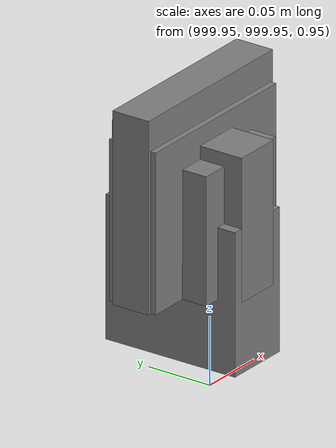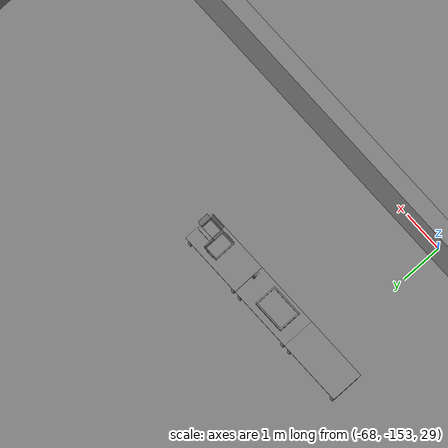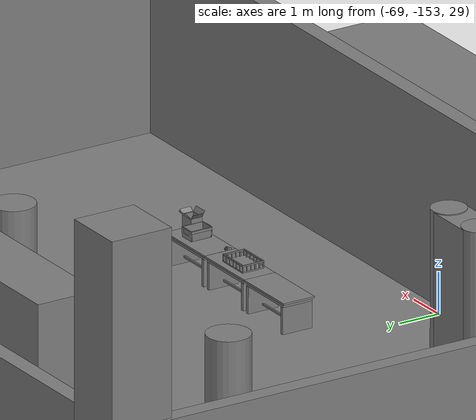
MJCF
<mujoco>
    <option gravity="0.000000000 0.000000000 -9.810000420" timestep="0.0049999999" integrator="implicitfast" density="1.225" viscosity="1.8000001e-05" noslip_iterations="10" iterations="100" sdf_iterations="50">
        <flag multiccd="disable"/>
    </option>
    <size memory="1000M"/>
    <compiler coordinate="local"/>
    <worldbody>
        <light cutoff="30" pos="0 1 1" dir="0 -1 -2"/>
        <light cutoff="30" pos="0 -1 1" dir="0 1 -2"/>
        <body pos="-64.866622925 -149.383972168 30.183746338" euler="89.999984741 89.999946594 0.000000000" name="openloong_gripper_2f85_fix_base_usda_bluebox_01">
            <geom contype="1" conaffinity="1" density="1000" type="box" material="" rgba="0.500000000 0.500000000 0.500000000 1.000000000" solimp="0.899999976 0.949999988 0.001000000" friction="1.000000000 0.005000000 0.000100000" solref="0.020000000 1.000000000" margin="0" condim="3" group="0" pos="0.276580811 0.187225342 0.000068665" quat="0.707106948 0.000077471 0.707106352 0.000077486" size="0.100000001 0.057999998 0.010000000" name="openloong_gripper_2f85_fix_base_usda_geom_B2568202_88F0_4DDC_860A_D740E5A4F013"/>
            <geom contype="1" conaffinity="1" density="1000" type="box" material="" rgba="0.500000000 0.500000000 0.500000000 1.000000000" solimp="0.899999976 0.949999988 0.001000000" friction="1.000000000 0.005000000 0.000100000" solref="0.020000000 1.000000000" margin="0" condim="3" group="0" pos="0.000000000 0.002883911 0.000000000" quat="0.999999881 0.000000000 0.000000000 0.000000000" size="0.254000008 0.003000000 0.172000006" name="openloong_gripper_2f85_fix_base_usda_geom_E1E52CB8_6084_4900_9385_DC457538CCBA"/>
            <geom contype="1" conaffinity="1" density="1000" type="box" material="" rgba="0.500000000 0.500000000 0.500000000 1.000000000" solimp="0.899999976 0.949999988 0.001000000" friction="1.000000000 0.005000000 0.000100000" solref="0.020000000 1.000000000" margin="0" condim="3" group="0" pos="0.000000000 0.124874115 0.173484802" quat="0.999796331 0.020176515 -0.000000015 0.000000030" size="0.259999990 0.119999997 0.007000000" name="openloong_gripper_2f85_fix_base_usda_geom_B93735BA_AA95_4F22_8737_A9DDE125302C"/>
            <geom contype="1" conaffinity="1" density="1000" type="box" material="" rgba="0.500000000 0.500000000 0.500000000 1.000000000" solimp="0.899999976 0.949999988 0.001000000" friction="1.000000000 0.005000000 0.000100000" solref="0.020000000 1.000000000" margin="0" condim="3" group="0" pos="0.000000000 0.124874115 -0.173469543" quat="0.999796331 -0.020176545 -0.000000015 0.000000000" size="0.259999990 0.119999997 0.007000000" name="openloong_gripper_2f85_fix_base_usda_geom_F2CB3CBA_DFAA_4B26_AF9E_6A620BDE7911"/>
            <geom contype="1" conaffinity="1" density="1000" type="box" material="" rgba="0.500000000 0.500000000 0.500000000 1.000000000" solimp="0.899999976 0.949999988 0.001000000" friction="1.000000000 0.005000000 0.000100000" solref="0.020000000 1.000000000" margin="0" condim="3" group="0" pos="0.000000000 0.214008331 0.188980103" quat="0.999912977 0.013176724 0.000000015 0.000000000" size="0.259999990 0.029999999 0.012500000" name="openloong_gripper_2f85_fix_base_usda_geom_572CAA60_1B03_4D4B_BD4B_CEAD34CBF7D3"/>
            <geom contype="1" conaffinity="1" density="1000" type="box" material="" rgba="0.500000000 0.500000000 0.500000000 1.000000000" solimp="0.899999976 0.949999988 0.001000000" friction="1.000000000 0.005000000 0.000100000" solref="0.020000000 1.000000000" margin="0" condim="3" group="0" pos="-0.258361816 0.125289917 0.001876831" quat="0.702796936 -0.020792112 0.710783124 0.020769298" size="0.189999998 0.119999997 0.009000000" name="openloong_gripper_2f85_fix_base_usda_geom_153509D2_50BC_41FE_9CC1_E237994AC01A"/>
            <geom contype="1" conaffinity="1" density="1000" type="box" material="" rgba="0.500000000 0.500000000 0.500000000 1.000000000" solimp="0.899999976 0.949999988 0.001000000" friction="1.000000000 0.005000000 0.000100000" solref="0.020000000 1.000000000" margin="0" condim="3" group="0" pos="0.000000000 0.214008331 -0.188980103" quat="0.999912977 -0.013176769 0.000000030 0.000000015" size="0.259999990 0.029999999 0.012500000" name="openloong_gripper_2f85_fix_base_usda_geom_1A12105D_99A7_4B53_A64A_E3257FFD78FC"/>
            <geom contype="1" conaffinity="1" density="1000" type="box" material="" rgba="0.500000000 0.500000000 0.500000000 1.000000000" solimp="0.899999976 0.949999988 0.001000000" friction="1.000000000 0.005000000 0.000100000" solref="0.020000000 1.000000000" margin="0" condim="3" group="0" pos="-0.276611328 0.187225342 0.000068665" quat="0.707106650 0.000077441 0.707106709 0.000077456" size="0.100000001 0.057999998 0.010000000" name="openloong_gripper_2f85_fix_base_usda_geom_A4CA5B27_3FC0_4C8B_9725_ADE544932A4F"/>
            <geom contype="1" conaffinity="1" density="1000" type="box" material="" rgba="0.500000000 0.500000000 0.500000000 1.000000000" solimp="0.899999976 0.949999988 0.001000000" friction="1.000000000 0.005000000 0.000100000" solref="0.020000000 1.000000000" margin="0" condim="3" group="0" pos="0.258331299 0.125289917 0.001876831" quat="0.702851415 0.018856421 0.710823774 -0.019329369" size="0.189999998 0.119999997 0.009000000" name="openloong_gripper_2f85_fix_base_usda_geom_D5E96494_7163_4ED8_A579_26FB0BC0E35A"/>
            <freejoint name="openloong_gripper_2f85_fix_base_usda_bluebox_01_joint"/>
            <site size="0.005000000 0.005000000 0.005000000" rgba="0.500000000 0.500000000 0.500000000 1.000000000" pos="0.000000000 0.000000000 0.000000000" quat="0.999961913 0.008726534 0.000000000 0.000000000" group="0" type="sphere" name="openloong_gripper_2f85_fix_base_usda_bluebox_01site"/>
        </body>
        <body pos="-64.496299744 -149.491867065 30.235729218" euler="0.000000000 0.000000000 89.999946594" name="openloong_gripper_2f85_fix_base_usda_cardboardbox_01">
            <geom contype="1" conaffinity="1" density="1000" type="box" material="" rgba="0.500000000 0.500000000 0.500000000 1.000000000" solimp="0.899999976 0.949999988 0.001000000" friction="1.000000000 0.005000000 0.000100000" solref="0.020000000 1.000000000" margin="0" condim="3" group="0" pos="-0.003166199 -0.004086494 0.005052090" quat="1.000000000 0.000000000 0.000000000 0.000000000" size="0.142499998 0.177500010 0.005000000" name="openloong_gripper_2f85_fix_base_usda_geom_148AA4C2_493F_4356_87CF_4C6B3E5BA88A"/>
            <geom contype="1" conaffinity="1" density="1000" type="box" material="" rgba="0.500000000 0.500000000 0.500000000 1.000000000" solimp="0.899999976 0.949999988 0.001000000" friction="1.000000000 0.005000000 0.000100000" solref="0.020000000 1.000000000" margin="0" condim="3" group="0" pos="-0.003166199 0.170316696 0.150570869" quat="1.000000000 0.000000000 0.000000000 0.000000000" size="0.142499998 0.005000000 0.149999991" name="openloong_gripper_2f85_fix_base_usda_geom_27C02C49_687C_40A9_8D5F_54C38F1E4D3F"/>
            <geom contype="1" conaffinity="1" density="1000" type="box" material="" rgba="0.500000000 0.500000000 0.500000000 1.000000000" solimp="0.899999976 0.949999988 0.001000000" friction="1.000000000 0.005000000 0.000100000" solref="0.020000000 1.000000000" margin="0" condim="3" group="0" pos="-0.147399902 -0.005307198 0.150570869" quat="1.000000000 0.000000000 0.000000000 0.000000000" size="0.005000000 0.177500010 0.149999991" name="openloong_gripper_2f85_fix_base_usda_geom_4079FD0B_B5AA_4681_B0E5_8F7D5B512F4E"/>
            <geom contype="1" conaffinity="1" density="1000" type="box" material="" rgba="0.500000000 0.500000000 0.500000000 1.000000000" solimp="0.899999976 0.949999988 0.001000000" friction="1.000000000 0.005000000 0.000100000" solref="0.020000000 1.000000000" margin="0" condim="3" group="0" pos="0.140275955 -0.005307198 0.150570869" quat="1.000000000 0.000000000 0.000000000 0.000000000" size="0.005000000 0.177500010 0.149999991" name="openloong_gripper_2f85_fix_base_usda_geom_65BD4C59_C1B0_4FA8_A8A9_E5FD0B3B4820"/>
            <geom contype="1" conaffinity="1" density="1000" type="box" material="" rgba="0.500000000 0.500000000 0.500000000 1.000000000" solimp="0.899999976 0.949999988 0.001000000" friction="1.000000000 0.005000000 0.000100000" solref="0.020000000 1.000000000" margin="0" condim="3" group="0" pos="-0.003166199 -0.181550980 0.150570869" quat="1.000000000 0.000000000 0.000000000 0.000000000" size="0.142499998 0.005000000 0.149999991" name="openloong_gripper_2f85_fix_base_usda_geom_CFE116C5_A05B_4813_ABD9_EED5EDE13875"/>
            <freejoint name="openloong_gripper_2f85_fix_base_usda_cardboardbox_01_joint"/>
            <site size="0.005000000 0.005000000 0.005000000" rgba="0.500000000 0.500000000 0.500000000 1.000000000" pos="0.000000000 0.000000000 0.000000000" quat="0.999961913 0.008726535 0.000000000 0.000000000" group="0" type="sphere" name="openloong_gripper_2f85_fix_base_usda_site_BBF8B8BA_CED2_4A1A_8A51_3BD81668C1F3"/>
            <body pos="0.139160156 -0.004048347 0.301930904" euler="-179.999954224 49.383502960 179.999954224" name="openloong_gripper_2f85_fix_base_usda_A1_006">
                <geom contype="1" conaffinity="1" density="1000" type="box" material="" rgba="0.500000000 0.500000000 0.500000000 1.000000000" solimp="0.899999976 0.949999988 0.001000000" friction="1.000000000 0.005000000 0.000100000" solref="0.020000000 1.000000000" margin="0" condim="3" group="0" pos="-0.071587563 0.000009537 0.001745224" quat="0.999999881 0.000000000 0.000000000 0.000000000" size="0.071249999 0.179999992 0.002500000" name="openloong_gripper_2f85_fix_base_usda_geom_85CE9461_7886_4BFE_94AB_8972F8074632"/>
                <joint armature="0" stiffness="0.07" damping="0.0099999998" axis="0.000000 1.000000 0.000000" type="hinge" name="openloong_gripper_2f85_fix_base_usda_A1_006"/>
            </body>
            <body pos="-0.145902634 -0.004086494 0.301938057" euler="-180.000000000 -60.000011444 -180.000000000" name="openloong_gripper_2f85_fix_base_usda_A2_006">
                <geom contype="1" conaffinity="1" density="1000" type="box" material="" rgba="0.500000000 0.500000000 0.500000000 1.000000000" solimp="0.899999976 0.949999988 0.001000000" friction="1.000000000 0.005000000 0.000100000" solref="0.020000000 1.000000000" margin="0" condim="3" group="0" pos="0.071268082 0.000009537 0.002717972" quat="0.000002921 0.000000000 -0.000000030 0.999999881" size="0.071249999 0.179999992 0.002500000" name="openloong_gripper_2f85_fix_base_usda_geom_D85A627C_FE29_442E_9F0C_4DE8C751A66B"/>
                <joint armature="0" stiffness="0.07" damping="0.0099999998" axis="0.000000 1.000000 0.000000" type="hinge" name="openloong_gripper_2f85_fix_base_usda_A2_006"/>
            </body>
            <body pos="-0.003385544 0.175991058 0.301930904" euler="-125.858116150 -0.000004561 0.000002331" name="openloong_gripper_2f85_fix_base_usda_B2_006">
                <geom contype="1" conaffinity="1" density="1000" type="box" material="" rgba="0.500000000 0.500000000 0.500000000 1.000000000" solimp="0.899999976 0.949999988 0.001000000" friction="1.000000000 0.005000000 0.000100000" solref="0.020000000 1.000000000" margin="0" condim="3" group="0" pos="0.000009537 -0.070939064 -0.002470016" quat="0.999614120 0.027776197 -0.000000015 0.000000030" size="0.137500003 0.064999998 0.005000000" name="openloong_gripper_2f85_fix_base_usda_geom_5F15CF71_36F7_4745_BC11_6C8E5B04F1DD"/>
                <joint armature="0" stiffness="0.07" damping="0.0099999998" axis="1.000000 0.000000 0.000000" type="hinge" name="openloong_gripper_2f85_fix_base_usda_B2_006"/>
            </body>
            <body pos="-0.003385544 -0.184140205 0.301938057" euler="147.805557251 0.000000000 0.000000000" name="openloong_gripper_2f85_fix_base_usda_B1_006">
                <geom contype="1" conaffinity="1" density="1000" type="box" material="" rgba="0.500000000 0.500000000 0.500000000 1.000000000" solimp="0.899999976 0.949999988 0.001000000" friction="1.000000000 0.005000000 0.000100000" solref="0.020000000 1.000000000" margin="0" condim="3" group="0" pos="-0.000028610 0.070202351 -0.002703667" quat="0.999614179 -0.027776167 0.000000000 0.000000000" size="0.137500003 0.064999998 0.005000000" name="openloong_gripper_2f85_fix_base_usda_geom_3F075170_78AE_44C4_B624_8DB3DC0DBF35"/>
                <joint armature="0" stiffness="0.07" damping="0.0099999998" axis="1.000000 0.000000 0.000000" type="hinge" name="openloong_gripper_2f85_fix_base_usda_B1_006"/>
            </body>
        </body>
        <body pos="-65.882858276 -149.481979370 30.229999542" euler="-64.487716675 0.000000000 0.000000000" name="openloong_gripper_2f85_fix_base_usda_Barcode">
            <geom contype="1" conaffinity="1" density="1000" type="box" material="" rgba="0.500000000 0.500000000 0.500000000 1.000000000" solimp="0.899999976 0.949999988 0.001000000" friction="1.000000000 0.005000000 0.000100000" solref="0.020000000 1.000000000" margin="0" condim="3" group="0" pos="0.000000000 0.013038635 0.001419067" quat="0.000000000 0.000000000 0.000000000 1.000000119" size="0.034000002 0.010000000 0.017999999" name="openloong_gripper_2f85_fix_base_usda_geom_93EAC776_2851_4508_BE60_421F4F7323AD"/>
            <geom contype="1" conaffinity="1" density="1000" type="box" material="" rgba="0.500000000 0.500000000 0.500000000 1.000000000" solimp="0.899999976 0.949999988 0.001000000" friction="1.000000000 0.005000000 0.000100000" solref="0.020000000 1.000000000" margin="0" condim="3" group="0" pos="0.000000000 -0.035301208 -0.007095337" quat="0.000000000 0.000000000 -0.043619365 0.999048233" size="0.028999999 0.010000000 0.020000000" name="openloong_gripper_2f85_fix_base_usda_geom_C970854E_A9E1_4A49_8319_426D9B9F4912"/>
            <geom contype="1" conaffinity="1" density="1000" type="box" material="" rgba="0.500000000 0.500000000 0.500000000 1.000000000" solimp="0.899999976 0.949999988 0.001000000" friction="1.000000000 0.005000000 0.000100000" solref="0.020000000 1.000000000" margin="0" condim="3" group="0" pos="0.000000000 -0.043411255 -0.011749268" quat="0.922262907 0.386563420 0.000000000 0.000000000" size="0.026000001 0.010000000 0.020000000" name="openloong_gripper_2f85_fix_base_usda_geom_11182B4F_81CF_4580_B273_E598C36BA3DF"/>
            <geom contype="1" conaffinity="1" density="1000" type="box" material="" rgba="0.500000000 0.500000000 0.500000000 1.000000000" solimp="0.899999976 0.949999988 0.001000000" friction="1.000000000 0.005000000 0.000100000" solref="0.020000000 1.000000000" margin="0" condim="3" group="0" pos="0.000000000 -0.016967773 -0.031860352" quat="0.000000000 0.000000000 0.000000000 1.000000119" size="0.008000000 0.010000000 0.013000000" name="openloong_gripper_2f85_fix_base_usda_geom_A868C790_1979_4343_8805_F1671AE24707"/>
            <geom contype="1" conaffinity="1" density="1000" type="box" material="" rgba="0.500000000 0.500000000 0.500000000 1.000000000" solimp="0.899999976 0.949999988 0.001000000" friction="1.000000000 0.005000000 0.000100000" solref="0.020000000 1.000000000" margin="0" condim="3" group="0" pos="0.000000000 -0.001869202 0.000312805" quat="0.953716993 0.300705761 0.000000000 0.000000000" size="0.032000002 0.010000000 0.018999999" name="openloong_gripper_2f85_fix_base_usda_geom_31A8F729_4B70_42B9_A8B0_E86EB9D120EA"/>
            <geom contype="1" conaffinity="1" density="1000" type="box" material="" rgba="0.500000000 0.500000000 0.500000000 1.000000000" solimp="0.899999976 0.949999988 0.001000000" friction="1.000000000 0.005000000 0.000100000" solref="0.020000000 1.000000000" margin="0" condim="3" group="0" pos="0.000000000 -0.019531250 -0.003173828" quat="0.953716993 0.300705761 0.000000000 0.000000000" size="0.030999999 0.010000000 0.020000000" name="openloong_gripper_2f85_fix_base_usda_geom_3A3293A1_FE09_4EB0_9616_7EBBCF239CF3"/>
            <geom contype="1" conaffinity="1" density="1000" type="box" material="" rgba="0.500000000 0.500000000 0.500000000 1.000000000" solimp="0.899999976 0.949999988 0.001000000" friction="1.000000000 0.005000000 0.000100000" solref="0.020000000 1.000000000" margin="0" condim="3" group="0" pos="0.000000000 -0.035301208 -0.007095337" quat="0.953716993 0.300705761 0.000000000 0.000000000" size="0.028999999 0.010000000 0.020000000" name="openloong_gripper_2f85_fix_base_usda_geom_4E28968A_765A_44C0_A35F_A4C867D60FC6"/>
            <geom contype="1" conaffinity="1" density="1000" type="box" material="" rgba="0.500000000 0.500000000 0.500000000 1.000000000" solimp="0.899999976 0.949999988 0.001000000" friction="1.000000000 0.005000000 0.000100000" solref="0.020000000 1.000000000" margin="0" condim="3" group="0" pos="0.000000000 -0.042617798 -0.071121216" quat="0.000000000 0.000000000 0.000000000 1.000000119" size="0.013000000 0.021000000 0.059999999" name="openloong_gripper_2f85_fix_base_usda_geom_2D39F818_83F3_410B_906A_D1903E127962"/>
            <freejoint name="openloong_gripper_2f85_fix_base_usda_Barcode_joint"/>
            <site size="0.005000000 0.005000000 0.005000000" rgba="0.500000000 0.500000000 0.500000000 1.000000000" pos="0.000000000 0.000000000 0.000000000" quat="1.000000000 0.000000000 0.000000000 0.000000000" group="0" type="sphere" name="openloong_gripper_2f85_fix_base_usda_Barcode_site"/>
        </body>
        <body pos="-66.745018005 -149.392349243 30.184000015" euler="0.000000000 0.000000000 89.999946594" name="[22330320855305]_Basket_01">
            <geom contype="1" conaffinity="1" density="1000" type="box" material="" rgba="0.500000000 0.500000000 0.500000000 1.000000000" solimp="0.899999976 0.949999988 0.001000000" friction="1.000000000 0.005000000 0.000100000" solref="0.020000000 1.000000000" margin="0" condim="3" group="0" pos="-0.052425385 0.389207840 0.089787483" quat="0.707107008 0.000000000 0.000000000 0.707106411" size="0.014249999 0.014249999 0.059999999" name="[22330320855305]_geom_06E0C263_D1F1_4E9E_A7B8_02628366049B"/>
            <geom contype="1" conaffinity="1" density="1000" type="box" material="" rgba="0.500000000 0.500000000 0.500000000 1.000000000" solimp="0.899999976 0.949999988 0.001000000" friction="1.000000000 0.005000000 0.000100000" solref="0.020000000 1.000000000" margin="0" condim="3" group="0" pos="0.264015198 -0.133043289 0.089787483" quat="0.707107008 0.000000000 0.000000000 0.707106411" size="0.014249999 0.014249999 0.059999999" name="[22330320855305]_geom_C2260D63_8995_41EB_B909_EC0DE518B20D"/>
            <geom contype="1" conaffinity="1" density="1000" type="box" material="" rgba="0.500000000 0.500000000 0.500000000 1.000000000" solimp="0.899999976 0.949999988 0.001000000" friction="1.000000000 0.005000000 0.000100000" solref="0.020000000 1.000000000" margin="0" condim="3" group="0" pos="-0.264015198 -0.265548706 0.089793205" quat="0.707107008 0.000000000 0.000000000 0.707106411" size="0.014249999 0.014249999 0.059999999" name="[22330320855305]_geom_16508C29_93A2_4147_A1D2_95065B7C317C"/>
            <geom contype="1" conaffinity="1" density="1000" type="box" material="" rgba="0.500000000 0.500000000 0.500000000 1.000000000" solimp="0.899999976 0.949999988 0.001000000" friction="1.000000000 0.005000000 0.000100000" solref="0.020000000 1.000000000" margin="0" condim="3" group="0" pos="-0.160263062 -0.389322281 0.089793205" quat="0.707107008 0.000000000 0.000000000 0.707106411" size="0.014249999 0.014249999 0.059999999" name="[22330320855305]_geom_944C3701_C6A4_4DC9_9334_BD279433F7B9"/>
            <geom contype="1" conaffinity="1" density="1000" type="box" material="" rgba="0.500000000 0.500000000 0.500000000 1.000000000" solimp="0.899999976 0.949999988 0.001000000" friction="1.000000000 0.005000000 0.000100000" solref="0.020000000 1.000000000" margin="0" condim="3" group="0" pos="0.162265778 -0.389322281 0.089787483" quat="0.707107008 0.000000000 0.000000000 0.707106411" size="0.014249999 0.014249999 0.059999999" name="[22330320855305]_geom_4AAF945C_577B_4F7C_A1CF_32403E801530"/>
            <geom contype="1" conaffinity="1" density="1000" type="box" material="" rgba="0.500000000 0.500000000 0.500000000 1.000000000" solimp="0.899999976 0.949999988 0.001000000" friction="1.000000000 0.005000000 0.000100000" solref="0.020000000 1.000000000" margin="0" condim="3" group="0" pos="0.264015198 0.389207840 0.089787483" quat="0.707107008 0.000000000 0.000000000 0.707106411" size="0.014249999 0.014249999 0.059999999" name="[22330320855305]_geom_DEDC6113_1E49_4E0F_853D_384A12ECF6EE"/>
            <geom contype="1" conaffinity="1" density="1000" type="box" material="" rgba="0.500000000 0.500000000 0.500000000 1.000000000" solimp="0.899999976 0.949999988 0.001000000" friction="1.000000000 0.005000000 0.000100000" solref="0.020000000 1.000000000" margin="0" condim="3" group="0" pos="-0.264015198 -0.133043289 0.089793205" quat="0.707107008 0.000000000 0.000000000 0.707106411" size="0.014249999 0.014249999 0.059999999" name="[22330320855305]_geom_0C8EBA63_A521_4EC0_95B9_1EF238F5B81D"/>
            <geom contype="1" conaffinity="1" density="1000" type="box" material="" rgba="0.500000000 0.500000000 0.500000000 1.000000000" solimp="0.899999976 0.949999988 0.001000000" friction="1.000000000 0.005000000 0.000100000" solref="0.020000000 1.000000000" margin="0" condim="3" group="0" pos="-0.264026642 0.269256592 0.089793205" quat="0.707107008 0.000000000 0.000000000 0.707106411" size="0.014249999 0.014249999 0.059999999" name="[22330320855305]_geom_2BCEC0DF_4368_4251_9ACE_8CE0149460C2"/>
            <geom contype="1" conaffinity="1" density="1000" type="box" material="" rgba="0.500000000 0.500000000 0.500000000 1.000000000" solimp="0.899999976 0.949999988 0.001000000" friction="1.000000000 0.005000000 0.000100000" solref="0.020000000 1.000000000" margin="0" condim="3" group="0" pos="0.054462433 0.389207840 0.089787483" quat="0.707107008 0.000000000 0.000000000 0.707106411" size="0.014249999 0.014249999 0.059999999" name="[22330320855305]_geom_10D5FC2E_A7F1_48EB_BF79_31FBDC57ABDA"/>
            <geom contype="1" conaffinity="1" density="1000" type="box" material="" rgba="0.500000000 0.500000000 0.500000000 1.000000000" solimp="0.899999976 0.949999988 0.001000000" friction="1.000000000 0.005000000 0.000100000" solref="0.020000000 1.000000000" margin="0" condim="3" group="0" pos="0.054462433 -0.389322281 0.089787483" quat="0.707107008 0.000000000 0.000000000 0.707106411" size="0.014249999 0.014249999 0.059999999" name="[22330320855305]_geom_C48DA1BB_1A71_4122_B16C_DF84320AA4C7"/>
            <geom contype="1" conaffinity="1" density="1000" type="box" material="" rgba="0.500000000 0.500000000 0.500000000 1.000000000" solimp="0.899999976 0.949999988 0.001000000" friction="1.000000000 0.005000000 0.000100000" solref="0.020000000 1.000000000" margin="0" condim="3" group="0" pos="0.264015198 0.269256592 0.089793205" quat="0.707107008 0.000000000 0.000000000 0.707106411" size="0.014249999 0.014249999 0.059999999" name="[22330320855305]_geom_A8590F80_85C9_44C4_92D2_465E1E0AA77A"/>
            <geom contype="1" conaffinity="1" density="1000" type="box" material="" rgba="0.500000000 0.500000000 0.500000000 1.000000000" solimp="0.899999976 0.949999988 0.001000000" friction="1.000000000 0.005000000 0.000100000" solref="0.020000000 1.000000000" margin="0" condim="3" group="0" pos="0.264015198 -0.389322281 0.089787483" quat="0.707107008 0.000000000 0.000000000 0.707106411" size="0.014249999 0.014249999 0.059999999" name="[22330320855305]_geom_68D1419C_55BE_489C_9DBB_F6C4B434D734"/>
            <geom contype="1" conaffinity="1" density="1000" type="box" material="" rgba="0.500000000 0.500000000 0.500000000 1.000000000" solimp="0.899999976 0.949999988 0.001000000" friction="1.000000000 0.005000000 0.000100000" solref="0.020000000 1.000000000" margin="0" condim="3" group="0" pos="0.000000000 0.000000000 0.015998840" quat="0.707107008 0.000000000 0.000000000 0.707106411" size="0.403499991 0.279000014 0.015750000" name="[22330320855305]_geom_19C75CE3_080A_429A_9BB4_FECC31989715"/>
            <geom contype="1" conaffinity="1" density="1000" type="box" material="" rgba="0.500000000 0.500000000 0.500000000 1.000000000" solimp="0.899999976 0.949999988 0.001000000" friction="1.000000000 0.005000000 0.000100000" solref="0.020000000 1.000000000" margin="0" condim="3" group="0" pos="0.000000000 -0.389476776 0.163619041" quat="0.707107008 0.000000000 0.000000000 0.707106411" size="0.015000000 0.277500004 0.015750000" name="[22330320855305]_geom_9BB6CBE8_A353_4F3E_A069_60864FFD8ADC"/>
            <geom contype="1" conaffinity="1" density="1000" type="box" material="" rgba="0.500000000 0.500000000 0.500000000 1.000000000" solimp="0.899999976 0.949999988 0.001000000" friction="1.000000000 0.005000000 0.000100000" solref="0.020000000 1.000000000" margin="0" condim="3" group="0" pos="0.162265778 0.389207840 0.089787483" quat="0.707107008 0.000000000 0.000000000 0.707106411" size="0.014249999 0.014249999 0.059999999" name="[22330320855305]_geom_5916937A_E742_42A5_BB1B_A386FB39C6B5"/>
            <geom contype="1" conaffinity="1" density="1000" type="box" material="" rgba="0.500000000 0.500000000 0.500000000 1.000000000" solimp="0.899999976 0.949999988 0.001000000" friction="1.000000000 0.005000000 0.000100000" solref="0.020000000 1.000000000" margin="0" condim="3" group="0" pos="0.000000000 0.389471054 0.163619041" quat="0.707107008 0.000000000 0.000000000 0.707106411" size="0.015000000 0.277500004 0.015750000" name="[22330320855305]_geom_28AA8DCE_4E52_4880_9B7C_BEC2F03E0575"/>
            <geom contype="1" conaffinity="1" density="1000" type="box" material="" rgba="0.500000000 0.500000000 0.500000000 1.000000000" solimp="0.899999976 0.949999988 0.001000000" friction="1.000000000 0.005000000 0.000100000" solref="0.020000000 1.000000000" margin="0" condim="3" group="0" pos="-0.263511658 0.000000000 0.163619041" quat="0.707107008 0.000000000 0.000000000 0.707106411" size="0.403499991 0.015000000 0.015750000" name="[22330320855305]_geom_6BBE4011_E4AF_4811_9778_812E178142E9"/>
            <geom contype="1" conaffinity="1" density="1000" type="box" material="" rgba="0.500000000 0.500000000 0.500000000 1.000000000" solimp="0.899999976 0.949999988 0.001000000" friction="1.000000000 0.005000000 0.000100000" solref="0.020000000 1.000000000" margin="0" condim="3" group="0" pos="-0.264015198 0.141334534 0.089793205" quat="0.707107008 0.000000000 0.000000000 0.707106411" size="0.014249999 0.014249999 0.059999999" name="[22330320855305]_geom_955B6811_5D5C_4002_B619_D86B10393B25"/>
            <geom contype="1" conaffinity="1" density="1000" type="box" material="" rgba="0.500000000 0.500000000 0.500000000 1.000000000" solimp="0.899999976 0.949999988 0.001000000" friction="1.000000000 0.005000000 0.000100000" solref="0.020000000 1.000000000" margin="0" condim="3" group="0" pos="0.264015198 -0.265548706 0.089787483" quat="0.707107008 0.000000000 0.000000000 0.707106411" size="0.014249999 0.014249999 0.059999999" name="[22330320855305]_geom_E6E48064_A125_497A_8351_68A86C69EE38"/>
            <geom contype="1" conaffinity="1" density="1000" type="box" material="" rgba="0.500000000 0.500000000 0.500000000 1.000000000" solimp="0.899999976 0.949999988 0.001000000" friction="1.000000000 0.005000000 0.000100000" solref="0.020000000 1.000000000" margin="0" condim="3" group="0" pos="-0.160263062 0.389207840 0.089787483" quat="0.707107008 0.000000000 0.000000000 0.707106411" size="0.014249999 0.014249999 0.059999999" name="[22330320855305]_geom_A28BA7A2_A32A_42EB_BADA_8FB484B2DB53"/>
            <geom contype="1" conaffinity="1" density="1000" type="box" material="" rgba="0.500000000 0.500000000 0.500000000 1.000000000" solimp="0.899999976 0.949999988 0.001000000" friction="1.000000000 0.005000000 0.000100000" solref="0.020000000 1.000000000" margin="0" condim="3" group="0" pos="-0.052425385 -0.389322281 0.089787483" quat="0.707107008 0.000000000 0.000000000 0.707106411" size="0.014249999 0.014249999 0.059999999" name="[22330320855305]_geom_6C236687_5383_435A_A08D_60C4152F7129"/>
            <geom contype="1" conaffinity="1" density="1000" type="box" material="" rgba="0.500000000 0.500000000 0.500000000 1.000000000" solimp="0.899999976 0.949999988 0.001000000" friction="1.000000000 0.005000000 0.000100000" solref="0.020000000 1.000000000" margin="0" condim="3" group="0" pos="-0.264026642 -0.389322281 0.089793205" quat="0.707107008 0.000000000 0.000000000 0.707106411" size="0.014249999 0.014249999 0.059999999" name="[22330320855305]_geom_1460DBCC_CF1E_43B7_A160_FA921668F0B6"/>
            <geom contype="1" conaffinity="1" density="1000" type="box" material="" rgba="0.500000000 0.500000000 0.500000000 1.000000000" solimp="0.899999976 0.949999988 0.001000000" friction="1.000000000 0.005000000 0.000100000" solref="0.020000000 1.000000000" margin="0" condim="3" group="0" pos="0.264015198 0.141334534 0.089787483" quat="0.707107008 0.000000000 0.000000000 0.707106411" size="0.014249999 0.014249999 0.059999999" name="[22330320855305]_geom_3F408F4B_18B1_4B07_8C16_211209A470D2"/>
            <geom contype="1" conaffinity="1" density="1000" type="box" material="" rgba="0.500000000 0.500000000 0.500000000 1.000000000" solimp="0.899999976 0.949999988 0.001000000" friction="1.000000000 0.005000000 0.000100000" solref="0.020000000 1.000000000" margin="0" condim="3" group="0" pos="-0.264015198 0.389207840 0.089793205" quat="0.707107008 0.000000000 0.000000000 0.707106411" size="0.014249999 0.014249999 0.059999999" name="[22330320855305]_geom_5A60273C_CE06_48FF_BFE2_324D99E1A0D6"/>
            <geom contype="1" conaffinity="1" density="1000" type="box" material="" rgba="0.500000000 0.500000000 0.500000000 1.000000000" solimp="0.899999976 0.949999988 0.001000000" friction="1.000000000 0.005000000 0.000100000" solref="0.020000000 1.000000000" margin="0" condim="3" group="0" pos="0.264015198 0.004480362 0.089787483" quat="0.707107008 0.000000000 0.000000000 0.707106411" size="0.014249999 0.014249999 0.059999999" name="[22330320855305]_geom_AE462A6F_6579_4F1F_B950_73779BFA9F4A"/>
            <geom contype="1" conaffinity="1" density="1000" type="box" material="" rgba="0.500000000 0.500000000 0.500000000 1.000000000" solimp="0.899999976 0.949999988 0.001000000" friction="1.000000000 0.005000000 0.000100000" solref="0.020000000 1.000000000" margin="0" condim="3" group="0" pos="0.263694763 -0.000011444 0.163619041" quat="0.707107008 0.000000000 0.000000000 0.707106411" size="0.403499991 0.015000000 0.015750000" name="[22330320855305]_geom_8B802260_DE03_48E3_BD55_5A836FA771F8"/>
            <geom contype="1" conaffinity="1" density="1000" type="box" material="" rgba="0.500000000 0.500000000 0.500000000 1.000000000" solimp="0.899999976 0.949999988 0.001000000" friction="1.000000000 0.005000000 0.000100000" solref="0.020000000 1.000000000" margin="0" condim="3" group="0" pos="-0.264015198 0.004480362 0.089793205" quat="0.707107008 0.000000000 0.000000000 0.707106411" size="0.014249999 0.014249999 0.059999999" name="[22330320855305]_geom_3C8259F8_AA2E_409B_AEDD_84F83B69F0F2"/>
            <freejoint name="[22330320855305]_joint_D6F98CB3_249D_4E75_9724_77DD7A4EB880"/>
        </body>
        <body pos="0.000000000 0.000000000 0.000000000" euler="0.000000000 0.000000000 0.000000000" name="Static Objects_Static Objects">
            <geom contype="1" conaffinity="1" density="1000" type="box" material="" rgba="0.500000000 0.500000000 0.500000000 1.000000000" solimp="0.899999976 0.949999988 0.001000000" friction="1.000000000 0.005000000 0.000100000" solref="0.020000000 1.000000000" margin="0" condim="3" group="0" pos="-67.544113159 -149.365814209 29.727830887" quat="0.500000417 0.499999970 0.499999553 0.499999970" size="0.381000012 0.319999993 0.041000001" name="Static Objects_geom_0712A02F_9FA0_492F_8757_32E7262B9B3C"/>
            <geom contype="1" conaffinity="1" density="1000" type="box" material="" rgba="0.500000000 0.500000000 0.500000000 1.000000000" solimp="0.899999976 0.949999988 0.001000000" friction="1.000000000 0.005000000 0.000100000" solref="0.020000000 1.000000000" margin="0" condim="3" group="0" pos="-68.239501953 -149.365814209 30.086868286" quat="0.500000417 0.499999970 0.499999553 0.499999970" size="0.370999992 0.039500002 0.745000005" name="Static Objects_geom_4BDBBDCF_38E3_4D4B_88C7_8DFD979CC250"/>
            <geom contype="1" conaffinity="1" density="1000" type="box" material="" rgba="0.500000000 0.500000000 0.500000000 1.000000000" solimp="0.899999976 0.949999988 0.001000000" friction="1.000000000 0.005000000 0.000100000" solref="0.020000000 1.000000000" margin="0" condim="3" group="0" pos="-68.239501953 -149.365814209 30.147235870" quat="0.500000417 0.499999970 0.499999553 0.499999970" size="0.400000006 0.022000000 0.800000012" name="Static Objects_geom_6AC87F91_0912_4965_972B_B201FFFA2540"/>
            <geom contype="1" conaffinity="1" density="1000" type="box" material="" rgba="0.500000000 0.500000000 0.500000000 1.000000000" solimp="0.899999976 0.949999988 0.001000000" friction="1.000000000 0.005000000 0.000100000" solref="0.020000000 1.000000000" margin="0" condim="3" group="0" pos="-68.934890747 -149.365814209 29.727830887" quat="0.500000417 0.499999970 0.499999553 0.499999970" size="0.381000012 0.319999993 0.041000001" name="Static Objects_geom_F6DA9821_0C86_4273_8D4B_2E4919FF943E"/>
            <geom contype="1" conaffinity="1" density="1000" type="box" material="" rgba="0.500000000 0.500000000 0.500000000 1.000000000" solimp="0.899999976 0.949999988 0.001000000" friction="1.000000000 0.005000000 0.000100000" solref="0.020000000 1.000000000" margin="0" condim="3" group="0" pos="-68.239501953 -149.365814209 29.561563492" quat="0.500000417 0.499999970 0.499999553 0.499999970" size="0.020000000 0.022000000 0.660000026" name="Static Objects_geom_52A17293_56D8_45E6_A8F3_DA905BC1AA4C"/>
            <geom contype="1" conaffinity="1" density="1000" type="box" material="" rgba="0.500000000 0.500000000 0.500000000 1.000000000" solimp="0.899999976 0.949999988 0.001000000" friction="1.000000000 0.005000000 0.000100000" solref="0.020000000 1.000000000" margin="0" condim="3" group="0" pos="-65.945671082 -149.365814209 29.727830887" quat="0.500000417 0.499999970 0.499999553 0.499999970" size="0.381000012 0.319999993 0.041000001" name="Static Objects_geom_FFEA0DC7_DAD0_434B_B259_5D69BBCB0BFD"/>
            <geom contype="1" conaffinity="1" density="1000" type="box" material="" rgba="0.500000000 0.500000000 0.500000000 1.000000000" solimp="0.899999976 0.949999988 0.001000000" friction="1.000000000 0.005000000 0.000100000" solref="0.020000000 1.000000000" margin="0" condim="3" group="0" pos="-66.641059875 -149.365814209 30.086868286" quat="0.500000417 0.499999970 0.499999553 0.499999970" size="0.370999992 0.039500002 0.745000005" name="Static Objects_geom_83D59C48_B78D_4A86_8997_CB8DA65E7D6B"/>
            <geom contype="1" conaffinity="1" density="1000" type="box" material="" rgba="0.500000000 0.500000000 0.500000000 1.000000000" solimp="0.899999976 0.949999988 0.001000000" friction="1.000000000 0.005000000 0.000100000" solref="0.020000000 1.000000000" margin="0" condim="3" group="0" pos="-66.641059875 -149.365814209 30.147235870" quat="0.500000417 0.499999970 0.499999553 0.499999970" size="0.400000006 0.022000000 0.800000012" name="Static Objects_geom_C00A187F_1D07_4224_A6A0_6E553E3528FC"/>
            <geom contype="1" conaffinity="1" density="1000" type="box" material="" rgba="0.500000000 0.500000000 0.500000000 1.000000000" solimp="0.899999976 0.949999988 0.001000000" friction="1.000000000 0.005000000 0.000100000" solref="0.020000000 1.000000000" margin="0" condim="3" group="0" pos="-67.336448669 -149.365814209 29.727830887" quat="0.500000417 0.499999970 0.499999553 0.499999970" size="0.381000012 0.319999993 0.041000001" name="Static Objects_geom_BFC1675C_BE2E_40DE_9096_6528B5F69946"/>
            <geom contype="1" conaffinity="1" density="1000" type="box" material="" rgba="0.500000000 0.500000000 0.500000000 1.000000000" solimp="0.899999976 0.949999988 0.001000000" friction="1.000000000 0.005000000 0.000100000" solref="0.020000000 1.000000000" margin="0" condim="3" group="0" pos="-66.641059875 -149.365814209 29.561563492" quat="0.500000417 0.499999970 0.499999553 0.499999970" size="0.020000000 0.022000000 0.660000026" name="Static Objects_geom_844EE0CC_0E0A_4C14_A9BB_99487A606327"/>
            <geom contype="1" conaffinity="1" density="1000" type="box" material="" rgba="0.500000000 0.500000000 0.500000000 1.000000000" solimp="0.899999976 0.949999988 0.001000000" friction="1.000000000 0.005000000 0.000100000" solref="0.020000000 1.000000000" margin="0" condim="3" group="0" pos="-64.338577271 -149.365814209 29.727830887" quat="0.500000417 0.499999970 0.499999553 0.499999970" size="0.381000012 0.319999993 0.041000001" name="Static Objects_geom_C24CD26F_463A_4E77_B410_99EFB755ADA0"/>
            <geom contype="1" conaffinity="1" density="1000" type="box" material="" rgba="0.500000000 0.500000000 0.500000000 1.000000000" solimp="0.899999976 0.949999988 0.001000000" friction="1.000000000 0.005000000 0.000100000" solref="0.020000000 1.000000000" margin="0" condim="3" group="0" pos="-65.033966064 -149.365814209 30.086868286" quat="0.500000417 0.499999970 0.499999553 0.499999970" size="0.370999992 0.039500002 0.745000005" name="Static Objects_geom_2A1A438B_6CC2_44C8_97C7_6982C938F3D9"/>
            <geom contype="1" conaffinity="1" density="1000" type="box" material="" rgba="0.500000000 0.500000000 0.500000000 1.000000000" solimp="0.899999976 0.949999988 0.001000000" friction="1.000000000 0.005000000 0.000100000" solref="0.020000000 1.000000000" margin="0" condim="3" group="0" pos="-65.033966064 -149.365814209 30.147235870" quat="0.500000417 0.499999970 0.499999553 0.499999970" size="0.400000006 0.022000000 0.800000012" name="Static Objects_geom_C9C52C8F_09AC_4DA5_A073_95E6F3E842E1"/>
            <geom contype="1" conaffinity="1" density="1000" type="box" material="" rgba="0.500000000 0.500000000 0.500000000 1.000000000" solimp="0.899999976 0.949999988 0.001000000" friction="1.000000000 0.005000000 0.000100000" solref="0.020000000 1.000000000" margin="0" condim="3" group="0" pos="-65.729354858 -149.365814209 29.727830887" quat="0.500000417 0.499999970 0.499999553 0.499999970" size="0.381000012 0.319999993 0.041000001" name="Static Objects_geom_3BE5AAA6_FB0B_4945_ACDA_0D3678916233"/>
            <geom contype="1" conaffinity="1" density="1000" type="box" material="" rgba="0.500000000 0.500000000 0.500000000 1.000000000" solimp="0.899999976 0.949999988 0.001000000" friction="1.000000000 0.005000000 0.000100000" solref="0.020000000 1.000000000" margin="0" condim="3" group="0" pos="-65.033966064 -149.365814209 29.561563492" quat="0.500000417 0.499999970 0.499999553 0.499999970" size="0.020000000 0.022000000 0.660000026" name="Static Objects_geom_178FB7A6_3501_4B7D_94CA_E55D87C730E0"/>
            <geom contype="1" conaffinity="1" density="1000" type="box" material="" rgba="0.500000000 0.500000000 0.500000000 1.000000000" solimp="0.899999976 0.949999988 0.001000000" friction="1.000000000 0.005000000 0.000100000" solref="0.020000000 1.000000000" margin="0" condim="3" group="0" pos="-61.754566193 -137.853729248 33.906845093" quat="0.707107067 0.000000000 0.000000000 0.707106471" size="0.759999990 0.759999990 4.500000000" name="Static Objects_geom_1BB18E1B_8DDC_4939_9FAD_37DF571BF7E9"/>
            <geom contype="1" conaffinity="1" density="1000" type="box" material="" rgba="0.500000000 0.500000000 0.500000000 1.000000000" solimp="0.899999976 0.949999988 0.001000000" friction="1.000000000 0.005000000 0.000100000" solref="0.020000000 1.000000000" margin="0" condim="3" group="0" pos="-57.511135101 -144.927108765 31.707921982" quat="1.000000000 0.000000000 0.000000000 0.000000000" size="0.200000003 8.000000000 2.299999952" name="Static Objects_geom_6FD94B5D_AB06_4A60_BDD3_9A95243F9455"/>
            <geom contype="1" conaffinity="1" density="1000" type="box" material="" rgba="0.500000000 0.500000000 0.500000000 1.000000000" solimp="0.899999976 0.949999988 0.001000000" friction="1.000000000 0.005000000 0.000100000" solref="0.020000000 1.000000000" margin="0" condim="3" group="0" pos="-80.517646790 -157.574050903 31.688196182" quat="0.707107067 0.000000000 0.000000000 0.707106471" size="0.600000024 0.600000024 2.299999952" name="Static Objects_geom_7CFC616E_B179_4AC3_A42B_C8198DAE758B"/>
            <geom contype="1" conaffinity="1" density="1000" type="box" material="" rgba="0.500000000 0.500000000 0.500000000 1.000000000" solimp="0.899999976 0.949999988 0.001000000" friction="1.000000000 0.005000000 0.000100000" solref="0.020000000 1.000000000" margin="0" condim="3" group="0" pos="-80.711044312 -147.414932251 31.666158676" quat="1.000000000 0.000000000 0.000000000 0.000000000" size="0.200000003 10.000000000 2.299999952" name="Static Objects_geom_2EA18C83_6807_4644_A9F1_AC7BA68798CD"/>
            <geom contype="1" conaffinity="1" density="1000" type="box" material="" rgba="0.500000000 0.500000000 0.500000000 1.000000000" solimp="0.899999976 0.949999988 0.001000000" friction="1.000000000 0.005000000 0.000100000" solref="0.020000000 1.000000000" margin="0" condim="3" group="0" pos="-57.687217712 -137.434692383 31.688196182" quat="0.707107067 0.000000000 0.000000000 0.707106471" size="0.600000024 0.600000024 2.299999952" name="Static Objects_geom_BF1FBE0A_7FE6_468C_B87A_A286C98ADCDA"/>
            <geom contype="1" conaffinity="1" density="1000" type="box" material="" rgba="0.500000000 0.500000000 0.500000000 1.000000000" solimp="0.899999976 0.949999988 0.001000000" friction="1.000000000 0.005000000 0.000100000" solref="0.020000000 1.000000000" margin="0" condim="3" group="0" pos="-69.537033081 -140.263229370 31.714921951" quat="0.707107067 0.000000000 0.000000000 0.707106471" size="0.759999990 4.500000000 2.299999952" name="Static Objects_geom_E6BB1097_538B_46B7_A835_2FD61265027B"/>
            <geom contype="1" conaffinity="1" density="1000" type="box" material="" rgba="0.500000000 0.500000000 0.500000000 1.000000000" solimp="0.899999976 0.949999988 0.001000000" friction="1.000000000 0.005000000 0.000100000" solref="0.020000000 1.000000000" margin="0" condim="3" group="0" pos="-80.073638916 -137.853713989 33.906845093" quat="0.707107067 0.000000000 0.000000000 0.707106471" size="0.759999990 0.759999990 4.500000000" name="Static Objects_geom_349024EF_CA16_411C_A295_A776B4228228"/>
            <geom contype="1" conaffinity="1" density="1000" type="box" material="" rgba="0.500000000 0.500000000 0.500000000 1.000000000" solimp="0.899999976 0.949999988 0.001000000" friction="1.000000000 0.005000000 0.000100000" solref="0.020000000 1.000000000" margin="0" condim="3" group="0" pos="-73.406707764 -155.734664917 31.707921982" quat="1.000000000 0.000000000 0.000000000 0.000000000" size="0.200000003 3.000000000 2.299999952" name="Static Objects_geom_7053B329_18AC_474C_A59D_F3E654F1F873"/>
            <geom contype="1" conaffinity="1" density="1000" type="box" material="" rgba="0.500000000 0.500000000 0.500000000 1.000000000" solimp="0.899999976 0.949999988 0.001000000" friction="1.000000000 0.005000000 0.000100000" solref="0.020000000 1.000000000" margin="0" condim="3" group="0" pos="-68.497543335 -137.448257446 31.707921982" quat="0.707107067 0.000000000 0.000000000 0.707106471" size="0.200000003 14.000000000 2.299999952" name="Static Objects_geom_B8D46E02_DAED_46D0_B6CE_B3E77B815FA6"/>
            <geom contype="1" conaffinity="1" density="1000" type="cylinder" material="" rgba="0.500000000 0.500000000 0.500000000 1.000000000" solimp="0.899999976 0.949999988 0.001000000" friction="1.000000000 0.005000000 0.000100000" solref="0.020000000 1.000000000" margin="0" condim="3" group="0" pos="-68.868522644 -142.134506226 31.711090088" quat="0.707107067 0.000000000 0.000000000 0.707106471" size="0.509999990 2.299999952 1.000000000" name="Static Objects_geom_911C2481_38DA_457E_8564_98512EF6959D"/>
            <geom contype="1" conaffinity="1" density="1000" type="plane" material="" rgba="0.500000000 0.500000000 0.500000000 1.000000000" solimp="0.899999976 0.949999988 0.001000000" friction="1.000000000 0.005000000 0.000100000" solref="0.020000000 1.000000000" margin="0" condim="3" group="0" pos="-72.873703003 -147.131927490 29.409669876" quat="1.000000000 0.000000000 0.000000000 0.000000000" size="18.000000000 14.000000000 1.000000000" name="Static Objects_geom_E70EF633_8D9C_4CAA_84C2_3CB132CE6E4A"/>
            <geom contype="1" conaffinity="1" density="1000" type="box" material="" rgba="0.500000000 0.500000000 0.500000000 1.000000000" solimp="0.899999976 0.949999988 0.001000000" friction="1.000000000 0.005000000 0.000100000" solref="0.020000000 1.000000000" margin="0" condim="3" group="0" pos="-79.943580627 -157.782272339 31.707921982" quat="0.707107067 0.000000000 0.000000000 0.707106471" size="0.200000003 7.000000000 2.299999952" name="Static Objects_geom_8FB3FE25_AC54_48F6_B645_BA805B85CFAF"/>
            <geom contype="1" conaffinity="1" density="1000" type="box" material="" rgba="0.500000000 0.500000000 0.500000000 1.000000000" solimp="0.899999976 0.949999988 0.001000000" friction="1.000000000 0.005000000 0.000100000" solref="0.020000000 1.000000000" margin="0" condim="3" group="0" pos="-65.421028137 -152.903442383 31.707921982" quat="0.707107067 0.000000000 0.000000000 0.707106471" size="0.200000003 7.800000191 2.299999952" name="Static Objects_geom_24D64780_4584_4F44_AAC1_1A265E234293"/>
            <geom contype="1" conaffinity="1" density="1000" type="box" material="" rgba="0.500000000 0.500000000 0.500000000 1.000000000" solimp="0.899999976 0.949999988 0.001000000" friction="1.000000000 0.005000000 0.000100000" solref="0.020000000 1.000000000" margin="0" condim="3" group="0" pos="-74.776908875 -149.964416504 31.688196182" quat="1.000000000 0.000000000 0.000000000 0.000000000" size="0.600000024 0.409999996 2.299999952" name="Static Objects_geom_0D0BEDD8_DE29_4B9B_963B_E84036D7E2F6"/>
            <geom contype="1" conaffinity="1" density="1000" type="cylinder" material="" rgba="0.500000000 0.500000000 0.500000000 1.000000000" solimp="0.899999976 0.949999988 0.001000000" friction="1.000000000 0.005000000 0.000100000" solref="0.020000000 1.000000000" margin="0" condim="3" group="0" pos="-60.161884308 -142.134506226 31.711090088" quat="0.707107067 0.000000000 0.000000000 0.707106471" size="0.509999990 2.299999952 1.000000000" name="Static Objects_geom_F88840B6_8055_4A6D_9815_4438FCF133C8"/>
            <geom contype="1" conaffinity="1" density="1000" type="cylinder" material="" rgba="0.500000000 0.500000000 0.500000000 1.000000000" solimp="0.899999976 0.949999988 0.001000000" friction="1.000000000 0.005000000 0.000100000" solref="0.020000000 1.000000000" margin="0" condim="3" group="0" pos="-75.382453918 -149.963455200 31.711090088" quat="0.707107067 0.000000000 0.000000000 0.707106471" size="0.409999996 2.299999952 1.000000000" name="Static Objects_geom_A0FACB9D_7421_4386_A750_0F5BFCB13447"/>
            <geom contype="1" conaffinity="1" density="1000" type="cylinder" material="" rgba="0.500000000 0.500000000 0.500000000 1.000000000" solimp="0.899999976 0.949999988 0.001000000" friction="1.000000000 0.005000000 0.000100000" solref="0.020000000 1.000000000" margin="0" condim="3" group="0" pos="-74.154960632 -149.963455200 31.711090088" quat="0.707107067 0.000000000 0.000000000 0.707106471" size="0.409999996 2.299999952 1.000000000" name="Static Objects_geom_75711D80_7619_4FE1_A993_296FEBDA0342"/>
            <geom contype="1" conaffinity="1" density="1000" type="cylinder" material="" rgba="0.500000000 0.500000000 0.500000000 1.000000000" solimp="0.899999976 0.949999988 0.001000000" friction="1.000000000 0.005000000 0.000100000" solref="0.020000000 1.000000000" margin="0" condim="3" group="0" pos="-77.566612244 -142.134506226 31.711090088" quat="0.707107067 0.000000000 0.000000000 0.707106471" size="0.509999990 2.299999952 1.000000000" name="Static Objects_geom_6E988764_349A_4A94_BB93_E2AB0A73808F"/>
        </body>
        <body pos="1000.000000000 1000.000000000 1.000000000" euler="0.000000000 0.000000000 180.000000000" name="openloong_gripper_2f85_fix_base_usda_battery_01">
            <geom contype="1" conaffinity="1" density="1000" type="box" material="" rgba="0.500000000 0.500000000 0.500000000 1.000000000" solimp="0.899999976 0.949999988 0.001000000" friction="1.000000000 0.005000000 0.000100000" solref="0.020000000 1.000000000" margin="0" condim="3" group="0" pos="-0.011123657 -0.041940309 0.101691343" quat="1.000000000 0.000000000 0.000000000 0.000000000" size="0.010800000 0.003375000 0.004725000" name="openloong_gripper_2f85_fix_base_usda_geom_79A42171_C283_42BD_A021_97BF9661A9C4"/>
            <geom contype="1" conaffinity="1" density="1000" type="box" material="" rgba="0.500000000 0.500000000 0.500000000 1.000000000" solimp="0.899999976 0.949999988 0.001000000" friction="1.000000000 0.005000000 0.000100000" solref="0.020000000 1.000000000" margin="0" condim="3" group="0" pos="-0.010876465 -0.044247437 0.047066893" quat="0.998702705 -0.050920475 0.000000000 0.000000000" size="0.009450001 0.002700000 0.024975000" name="openloong_gripper_2f85_fix_base_usda_geom_86A5C65B_4D93_478E_A52C_43EA8D72FF68"/>
            <geom contype="1" conaffinity="1" density="1000" type="box" material="" rgba="0.500000000 0.500000000 0.500000000 1.000000000" solimp="0.899999976 0.949999988 0.001000000" friction="1.000000000 0.005000000 0.000100000" solref="0.020000000 1.000000000" margin="0" condim="3" group="0" pos="-0.001235962 -0.000659180 0.047381196" quat="1.000000000 0.000000000 0.000000000 0.000000000" size="0.039420001 0.039150000 0.047250003" name="openloong_gripper_2f85_fix_base_usda_geom_A4F2EE29_232C_4C9F_8D45_66C5E44973C0"/>
            <geom contype="1" conaffinity="1" density="1000" type="box" material="" rgba="0.500000000 0.500000000 0.500000000 1.000000000" solimp="0.899999976 0.949999988 0.001000000" friction="1.000000000 0.005000000 0.000100000" solref="0.020000000 1.000000000" margin="0" condim="3" group="0" pos="-0.010876465 -0.039138794 0.009851727" quat="1.000000000 0.000000000 0.000000000 0.000000000" size="0.009450001 0.010800000 0.013500000" name="openloong_gripper_2f85_fix_base_usda_geom_DF1511A1_56C6_40D1_AEDB_E375C37FBEE2"/>
            <geom contype="1" conaffinity="1" density="1000" type="box" material="" rgba="0.500000000 0.500000000 0.500000000 1.000000000" solimp="0.899999976 0.949999988 0.001000000" friction="1.000000000 0.005000000 0.000100000" solref="0.020000000 1.000000000" margin="0" condim="3" group="0" pos="-0.010876465 -0.041528322 0.071508206" quat="1.000000000 0.000000000 0.000000000 0.000000000" size="0.009450001 0.002700000 0.027000001" name="openloong_gripper_2f85_fix_base_usda_geom_C33496BB_F7A2_49BE_B2BF_6F93CB0CE15C"/>
            <freejoint name="openloong_gripper_2f85_fix_base_usda_battery_01_joint"/>
            <site size="0.005000000 0.005000000 0.005000000" rgba="0.500000000 0.500000000 0.500000000 1.000000000" pos="0.000000000 0.000000000 0.000000000" quat="0.999961913 0.008726500 0.000000000 0.000000000" group="0" type="sphere" name="openloong_gripper_2f85_fix_base_usda_battery_01site"/>
        </body>
        <body pos="1000.000000000 1000.000000000 1.000000000" euler="0.000000000 0.000000000 180.000000000" name="openloong_gripper_2f85_fix_base_usda_cpu_fan">
            <geom contype="1" conaffinity="1" density="1000" type="box" material="" rgba="0.500000000 0.500000000 0.500000000 1.000000000" solimp="0.899999976 0.949999988 0.001000000" friction="1.000000000 0.005000000 0.000100000" solref="0.020000000 1.000000000" margin="0" condim="3" group="0" pos="0.000000000 0.000000000 0.070034981" quat="0.000000000 0.000000000 0.000000000 1.000000000" size="0.070700005 0.014699999 0.070700005" name="openloong_gripper_2f85_fix_base_usda_geom_09BCE519_6F9E_44E7_9B8C_1F178C33CB57"/>
            <freejoint name="openloong_gripper_2f85_fix_base_usda_cpu_fan_joint"/>
            <site size="0.005000000 0.005000000 0.005000000" rgba="0.500000000 0.500000000 0.500000000 1.000000000" pos="0.000000000 0.000000000 0.000000000" quat="0.999961913 0.008726535 0.000000000 0.000000000" group="0" type="sphere" name="openloong_gripper_2f85_fix_base_usda_cpu_fancsite"/>
        </body>
        <body pos="1000.000000000 1000.000000000 1.000000000" euler="0.000000000 0.000000000 180.000000000" name="openloong_gripper_2f85_fix_base_usda_wifi_box">
            <geom contype="1" conaffinity="1" density="1000" type="box" material="" rgba="0.500000000 0.500000000 0.500000000 1.000000000" solimp="0.899999976 0.949999988 0.001000000" friction="1.000000000 0.005000000 0.000100000" solref="0.020000000 1.000000000" margin="0" condim="3" group="0" pos="0.000000000 0.000000000 0.058978677" quat="0.000000000 0.000000047 0.000000000 1.000000000" size="0.068499997 0.018999999 0.059000000" name="openloong_gripper_2f85_fix_base_usda_geom_D8A96832_3130_4A57_98D5_7C21A919E489"/>
            <freejoint name="openloong_gripper_2f85_fix_base_usda_wifi_box_joint"/>
            <site size="0.005000000 0.005000000 0.005000000" rgba="0.500000000 0.500000000 0.500000000 1.000000000" pos="0.000000000 0.000000000 0.000000000" quat="0.999961913 0.008726500 0.000000000 0.000000000" group="0" type="sphere" name="openloong_gripper_2f85_fix_base_usda_wifi_boxsite"/>
        </body>
        <body pos="-65.803222656 -149.616317749 31.166807175" euler="109.493736267 -38.708133698 166.809860229" mocap="true" name="spotlight6_SpotLight"/>
        <body pos="1000.000000000 1000.000000000 1.000000000" euler="0.000011953 0.000005123 -179.999984741" name="openloong_gripper_2f85_fix_base_usda_intel_box">
            <geom contype="1" conaffinity="1" density="1000" type="box" material="" rgba="0.500000000 0.500000000 0.500000000 1.000000000" solimp="0.899999976 0.949999988 0.001000000" friction="1.000000000 0.005000000 0.000100000" solref="0.020000000 1.000000000" margin="0" condim="3" group="0" pos="0.000000000 -0.000067139 0.000082284" quat="0.707106709 0.000000225 0.000000253 0.707106650" size="0.052800003 0.025300000 0.052800003" name="openloong_gripper_2f85_fix_base_usda_geom_04C40018_4375_415F_8662_D406FF5CADD7"/>
            <freejoint name="openloong_gripper_2f85_fix_base_usda_intel_box_joint"/>
            <site size="0.005000000 0.005000000 0.005000000" rgba="0.500000000 0.500000000 0.500000000 1.000000000" pos="0.000000000 0.000000000 0.000000000" quat="0.999961913 0.008726500 0.000000000 0.000000000" group="0" type="sphere" name="openloong_gripper_2f85_fix_base_usda_intel_boxsite"/>
        </body>
        <body pos="-66.359062195 -149.347595215 31.164068222" euler="117.755744934 -35.386409760 153.286132812" mocap="true" name="spotlight5_SpotLight"/>
        <body pos="1000.000000000 999.999938965 1.000000000" euler="0.000000000 0.000000000 180.000000000" name="openloong_gripper_2f85_fix_base_usda_intelcore_i5">
            <geom contype="1" conaffinity="1" density="1000" type="box" material="" rgba="0.500000000 0.500000000 0.500000000 1.000000000" solimp="0.899999976 0.949999988 0.001000000" friction="1.000000000 0.005000000 0.000100000" solref="0.020000000 1.000000000" margin="0" condim="3" group="0" pos="0.000000000 0.000000000 0.051722717" quat="0.707106709 0.000000000 0.000000000 -0.707106769" size="0.052800000 0.018080002 0.052800000" name="openloong_gripper_2f85_fix_base_usda_geom_E740448F_DE34_448C_9389_5E863E02A458"/>
            <freejoint name="openloong_gripper_2f85_fix_base_usda_intelcore_i5_joint"/>
            <site size="0.005000000 0.005000000 0.005000000" rgba="0.500000000 0.500000000 0.500000000 1.000000000" pos="0.000000000 0.000000000 0.000000000" quat="0.999961913 0.008726534 0.000000000 0.000000000" group="0" type="sphere" name="openloong_gripper_2f85_fix_base_usda_intelcore_i5site"/>
        </body>
        <body pos="-65.950607300 -149.757110596 31.164127350" euler="165.579681396 -63.430152893 89.904411316" mocap="true" name="spotlight1_SpotLight"/>
        <body pos="-66.291030884 -149.869689941 29.018842697" euler="0.000000000 0.000000000 89.999946594" mocap="true" name="openloong_gripper_2f85_fix_base_usda_leftHandMocap"/>
        <body pos="-66.291030884 -149.869689941 29.018842697" euler="0.000000000 0.000000000 89.999946594" mocap="true" name="openloong_gripper_2f85_fix_base_usda_rightHandMocap"/>
        <body pos="-66.291030884 -149.869689941 30.218843460" euler="0.000000000 0.000000000 89.999946594" name="openloong_gripper_2f85_fix_base_usda_base_link">
            <geom contype="1" conaffinity="1" density="1000" type="mesh" material="" rgba="0.783999979 0.783999979 0.783999979 1.000000000" solimp="0.899999976 0.949999988 0.001000000" friction="1.000000000 0.005000000 0.000100000" solref="0.020000000 1.000000000" margin="0" condim="3" group="3" mesh="base_link" pos="0.000000000 0.000000000 0.000000000" quat="1.000000000 0.000000000 0.000000000 0.000000000" size="1.000000000 1.000000000 1.000000000" name="openloong_gripper_2f85_fix_base_usda__geom_7_951A02BE_7A9B_4C1E_A978_07FA4F2412B9"/>
            <site size="0.005000000 0.005000000 0.005000000" rgba="0.500000000 0.500000000 0.500000000 1.000000000" pos="0.000000000 0.000000000 0.000000000" quat="1.000000000 0.000000000 0.000000000 0.000000000" group="0" type="sphere" name="openloong_gripper_2f85_fix_base_usda_imu"/>
            <inertial mass="22.447001" pos="-0.005664100 -0.001336700 0.238289997" diaginertia="0.374352545 0.277180195 0.220617250" quat="0.999247074 0.035235517 -0.015086859 0.006023135"/>
            <body pos="0.000000000 0.000000000 0.299997330" euler="0.000000000 0.000000000 0.000000000" name="openloong_gripper_2f85_fix_base_usda_dummy_body">
                <geom contype="1" conaffinity="1" density="1000" type="sphere" material="" rgba="0.783999979 0.783999979 0.783999979 1.000000000" solimp="0.899999976 0.949999988 0.001000000" friction="1.000000000 0.005000000 0.000100000" solref="0.020000000 1.000000000" margin="0" condim="3" group="3" pos="0.000000000 0.000000000 0.000000000" quat="1.000000000 0.000000000 0.000000000 0.000000000" size="0.010000000 0.000000000 0.000000000" name="openloong_gripper_2f85_fix_base_usda__geom_8_FE6B9F56_5BC0_45E4_97DE_34DF8C1A7EE7"/>
                <joint armature="0.0099999998" stiffness="0" damping="0.1" axis="0.000000 0.000000 1.000000" type="hinge" name="openloong_gripper_2f85_fix_base_usda_dummy_joint"/>
                <site size="0.010000000 0.005000000 0.005000000" rgba="0.500000000 0.500000000 0.500000000 1.000000000" pos="0.000000000 0.000000000 0.000000000" quat="1.000000000 0.000000000 0.000000000 0.000000000" group="3" type="sphere" name="openloong_gripper_2f85_fix_base_usda_dummy_site"/>
            </body>
            <body pos="0.009002686 0.000000000 0.406400681" euler="0.000000000 0.000000000 0.000000000" name="openloong_gripper_2f85_fix_base_usda_Link_head_yaw">
                <geom contype="1" conaffinity="1" density="1000" type="mesh" material="" rgba="0.783999979 0.783999979 0.783999979 1.000000000" solimp="0.899999976 0.949999988 0.001000000" friction="1.000000000 0.005000000 0.000100000" solref="0.020000000 1.000000000" margin="0" condim="3" group="3" mesh="Link_head_yaw" pos="0.000000000 0.000000000 0.000000000" quat="1.000000000 0.000000000 0.000000000 0.000000000" size="1.000000000 1.000000000 1.000000000" name="openloong_gripper_2f85_fix_base_usda__geom_10_1B01CAB4_912D_4F23_B952_AC24532C9AEA"/>
                <inertial mass="0.84249002" pos="0.000000000 -0.002081400 0.044801001" diaginertia="0.000700588 0.000629000 0.000553812" quat="0.706933022 -0.015675601 0.015677100 0.706933022"/>
                <body pos="0.000000000 -0.034599304 0.048500061" euler="0.000000000 0.000000000 0.000000000" name="openloong_gripper_2f85_fix_base_usda_Link_head_pitch">
                    <geom contype="1" conaffinity="1" density="1000" type="mesh" material="" rgba="0.783999979 0.783999979 0.783999979 1.000000000" solimp="0.899999976 0.949999988 0.001000000" friction="1.000000000 0.005000000 0.000100000" solref="0.020000000 1.000000000" margin="0" condim="3" group="3" mesh="Link_head_pitch" pos="0.000000000 0.000000000 0.000000000" quat="1.000000000 0.000000000 0.000000000 0.000000000" size="1.000000000 1.000000000 1.000000000" name="openloong_gripper_2f85_fix_base_usda__geom_12_E4A4D47A_0096_4492_AFE1_EE6B34B1F16E"/>
                    <inertial mass="1.3943" pos="0.020569000 0.033004001 0.125000000" diaginertia="0.006381400 0.006289940 0.004481460" quat="0.973390222 0.008406822 0.228157058 0.019624906"/>
                    <body pos="0.000000000 0.029998779 0.000000000" euler="0.000000000 0.000000000 0.000000000" name="openloong_gripper_2f85_fix_base_usda_neck_center_body">
                        <site size="0.010000000 0.005000000 0.005000000" rgba="0.500000000 0.500000000 0.500000000 1.000000000" pos="0.000000000 0.000000000 0.000000000" quat="1.000000000 0.000000000 0.000000000 0.000000000" group="3" type="sphere" name="openloong_gripper_2f85_fix_base_usda_neck_center_site"/>
                        <body pos="0.020004272 0.000000000 0.149999619" euler="-0.000002229 39.998176575 -90.000205994" name="openloong_gripper_2f85_fix_base_usda_camera_head">
                            <site size="0.010000000 0.005000000 0.005000000" rgba="0.500000000 0.500000000 0.500000000 1.000000000" pos="0.000000000 0.000000000 0.000000000" quat="1.000000000 0.000000000 0.000000000 0.000000000" group="3" type="sphere" name="openloong_gripper_2f85_fix_base_usda_camera_head_site"/>
                        </body>
                    </body>
                </body>
            </body>
            <body pos="0.003997803 -0.161598206 0.392200470" euler="0.000000000 0.000000000 0.000000000" name="openloong_gripper_2f85_fix_base_usda_Link_arm_r_01">
                <geom contype="1" conaffinity="1" density="1000" type="mesh" material="" rgba="0.783999979 0.783999979 0.783999979 1.000000000" solimp="0.899999976 0.949999988 0.001000000" friction="1.000000000 0.005000000 0.000100000" solref="0.020000000 1.000000000" margin="0" condim="3" group="3" mesh="Link_arm_r_01" pos="0.000000000 0.000000000 0.000000000" quat="1.000000000 0.000000000 0.000000000 0.000000000" size="1.000000000 1.000000000 1.000000000" name="openloong_gripper_2f85_fix_base_usda__geom_14_A44877DD_4566_4CD6_9636_B0758F792EEF"/>
                <joint armature="0.0099999998" stiffness="0" damping="1" axis="0.000000 -1.000000 0.000000" limited="true" range="-170.000015259 170.000015259" type="hinge" name="openloong_gripper_2f85_fix_base_usda_J_arm_r_01"/>
                <inertial mass="0.75641" pos="0.004494600 -0.038293999 -0.000001874" diaginertia="0.000842990 0.000803050 0.000587120" quat="-0.000163502 0.707098067 0.000812463 0.707115054"/>
                <body pos="-0.041992188 -0.041000366 0.000000000" euler="0.000000000 0.000000000 0.000000000" name="openloong_gripper_2f85_fix_base_usda_Link_arm_r_02">
                    <geom contype="1" conaffinity="1" density="1000" type="mesh" material="" rgba="0.783999979 0.783999979 0.783999979 1.000000000" solimp="0.899999976 0.949999988 0.001000000" friction="1.000000000 0.005000000 0.000100000" solref="0.020000000 1.000000000" margin="0" condim="3" group="3" mesh="Link_arm_r_02" pos="0.000000000 0.000000000 0.000000000" quat="1.000000000 0.000000000 0.000000000 0.000000000" size="1.000000000 1.000000000 1.000000000" name="openloong_gripper_2f85_fix_base_usda__geom_16_92B4188A_F952_471B_A801_F8E898890929"/>
                    <joint armature="0.0099999998" stiffness="0" damping="1" axis="-1.000000 0.000000 0.000000" limited="true" range="-105.000244141 105.000244141" type="hinge" name="openloong_gripper_2f85_fix_base_usda_J_arm_r_02"/>
                    <inertial mass="0.98500001" pos="0.041999999 -0.067430697 0.000000000" diaginertia="0.002262690 0.001730990 0.001154020" quat="0.500000000 0.500000000 -0.500000000 0.500000000"/>
                    <body pos="0.041992188 -0.122596741 0.000000000" euler="0.000000000 0.000000000 0.000000000" name="openloong_gripper_2f85_fix_base_usda_Link_arm_r_03">
                        <geom contype="1" conaffinity="1" density="1000" type="mesh" material="" rgba="0.783999979 0.783999979 0.783999979 1.000000000" solimp="0.899999976 0.949999988 0.001000000" friction="1.000000000 0.005000000 0.000100000" solref="0.020000000 1.000000000" margin="0" condim="3" group="3" mesh="Link_arm_r_03" pos="0.000000000 0.000000000 0.000000000" quat="1.000000000 0.000000000 0.000000000 0.000000000" size="1.000000000 1.000000000 1.000000000" name="openloong_gripper_2f85_fix_base_usda__geom_18_65D35212_2452_42D2_B78E_A1F49E26AC3A"/>
                        <joint armature="0.0099999998" stiffness="0" damping="1" axis="0.000000 -1.000000 0.000000" limited="true" range="-170.000015259 170.000015259" type="hinge" name="openloong_gripper_2f85_fix_base_usda_J_arm_r_03"/>
                        <inertial mass="0.95899999" pos="-0.001413580 -0.164663002 0.020757901" diaginertia="0.002101340 0.002064590 0.000754802" quat="0.560480952 0.454391927 -0.443732947 0.531497955"/>
                        <body pos="0.035293579 -0.177406311 0.023998260" euler="0.000000000 0.000000000 0.000000000" name="openloong_gripper_2f85_fix_base_usda_Link_arm_r_04">
                            <geom contype="1" conaffinity="1" density="1000" type="mesh" material="" rgba="0.783999979 0.783999979 0.783999979 1.000000000" solimp="0.899999976 0.949999988 0.001000000" friction="1.000000000 0.005000000 0.000100000" solref="0.020000000 1.000000000" margin="0" condim="3" group="3" mesh="Link_arm_r_04" pos="0.000000000 0.000000000 0.000000000" quat="1.000000000 0.000000000 0.000000000 0.000000000" size="1.000000000 1.000000000 1.000000000" name="openloong_gripper_2f85_fix_base_usda__geom_20_C0E718E9_E533_489B_A9ED_B56FD1B05096"/>
                            <joint armature="0.0099999998" stiffness="0" damping="1" axis="-1.000000 0.000000 0.000000" limited="true" range="0.000000000 170.000015259" type="hinge" name="openloong_gripper_2f85_fix_base_usda_J_arm_r_04"/>
                            <inertial mass="0.60000002" pos="-0.038727000 -0.060766999 -0.021003000" diaginertia="0.001092610 0.000712422 0.000645102" quat="0.327701002 0.632602990 -0.467366993 0.523443997"/>
                            <body pos="-0.035293579 -0.103492737 -0.023998260" euler="0.000000000 0.000000000 0.000000000" name="openloong_gripper_2f85_fix_base_usda_Link_arm_r_05">
                                <geom contype="1" conaffinity="1" density="1000" type="mesh" material="" rgba="0.783999979 0.783999979 0.783999979 1.000000000" solimp="0.899999976 0.949999988 0.001000000" friction="1.000000000 0.005000000 0.000100000" solref="0.020000000 1.000000000" margin="0" condim="3" group="3" mesh="Link_arm_r_05" pos="0.000000000 0.000000000 0.000000000" quat="1.000000000 0.000000000 0.000000000 0.000000000" size="1.000000000 1.000000000 1.000000000" name="openloong_gripper_2f85_fix_base_usda__geom_22_D0002662_B312_4AF4_BA83_ECF40F9435DB"/>
                                <joint armature="0.0099999998" stiffness="0" damping="1" axis="0.000000 -1.000000 0.000000" limited="true" range="-170.000015259 170.000015259" type="hinge" name="openloong_gripper_2f85_fix_base_usda_J_arm_r_05"/>
                                <inertial mass="0.68976003" pos="0.000032712 -0.068658002 -0.000111780" diaginertia="0.002522510 0.002411100 0.000448695" quat="0.707660973 0.706543028 -0.002603360 0.002470550"/>
                                <body pos="-0.026489258 -0.196502686 0.000000000" euler="0.000000000 0.000000000 0.000000000" name="openloong_gripper_2f85_fix_base_usda_Link_arm_r_06">
                                    <geom contype="1" conaffinity="1" density="1000" type="mesh" material="" rgba="0.783999979 0.783999979 0.783999979 1.000000000" solimp="0.899999976 0.949999988 0.001000000" friction="1.000000000 0.005000000 0.000100000" solref="0.020000000 1.000000000" margin="0" condim="3" group="3" mesh="Link_arm_r_06" pos="0.000000000 0.000000000 0.000000000" quat="1.000000000 0.000000000 0.000000000 0.000000000" size="1.000000000 1.000000000 1.000000000" name="openloong_gripper_2f85_fix_base_usda__geom_24_2D7270A1_44B0_442F_A5BA_C2F186D4C028"/>
                                    <joint armature="0.0099999998" stiffness="0" damping="1" axis="1.000000 0.000000 0.000000" limited="true" range="-105.000244141 105.000244141" type="hinge" name="openloong_gripper_2f85_fix_base_usda_J_arm_r_06"/>
                                    <inertial mass="0.28" pos="0.026078001 -0.000000896 0.001663700" diaginertia="0.000156930 0.000145601 0.000104979" quat="0.707080841 0.001851080 0.001883810 0.707127810"/>
                                    <body pos="0.026489258 0.000000000 0.031799316" euler="0.000000000 0.000000000 0.000000000" name="openloong_gripper_2f85_fix_base_usda_Link_arm_r_07">
                                        <geom contype="1" conaffinity="1" density="1000" type="mesh" material="" rgba="0.783999979 0.783999979 0.783999979 1.000000000" solimp="0.899999976 0.949999988 0.001000000" friction="1.000000000 0.005000000 0.000100000" solref="0.020000000 1.000000000" margin="0" condim="3" group="3" mesh="Link_arm_r_07" pos="0.000000000 0.000000000 0.000000000" quat="1.000000000 0.000000000 0.000000000 0.000000000" size="1.000000000 1.000000000 1.000000000" name="openloong_gripper_2f85_fix_base_usda__geom_26_D6606D24_F02A_477B_BC33_4079BFB0EA52"/>
                                        <joint armature="0.0099999998" stiffness="0" damping="1" axis="0.000000 0.000000 1.000000" limited="true" range="-60.000133514 60.000133514" type="hinge" name="openloong_gripper_2f85_fix_base_usda_J_arm_r_07"/>
                                        <inertial mass="0.61353999" pos="-0.007859000 -0.158170000 -0.027736001" diaginertia="0.003037610 0.002570910 0.000729379" quat="0.427542925 0.443532884 -0.553093910 0.560867906"/>
                                        <body pos="0.000000000 0.286994934 -0.270000458" euler="150.000350952 -0.000001649 -0.000000442" name="openloong_gripper_2f85_fix_base_usda_camera_wrist_r">
                                            <site size="0.010000000 0.005000000 0.005000000" rgba="0.500000000 0.500000000 0.500000000 1.000000000" pos="0.000000000 0.000000000 0.000000000" quat="1.000000000 0.000000000 0.000000000 0.000000000" group="3" type="sphere" name="openloong_gripper_2f85_fix_base_usda_camera_wrist_r_site"/>
                                        </body>
                                        <body pos="0.000000000 -0.220008850 -0.033002853" euler="0.000000000 0.000000000 179.999969482" name="openloong_gripper_2f85_fix_base_usda_ee_center_body_r">
                                            <site size="0.010000000 0.005000000 0.005000000" rgba="0.500000000 0.500000000 0.500000000 1.000000000" pos="0.000000000 0.000000000 0.000000000" quat="1.000000000 0.000000000 0.000000000 0.000000000" group="3" type="sphere" name="openloong_gripper_2f85_fix_base_usda_ee_center_site_r"/>
                                        </body>
                                        <body pos="0.000000000 -0.066001892 -0.031000137" euler="89.999984741 0.000000000 180.000000000" name="openloong_gripper_2f85_fix_base_usda_zbr_base_link">
                                            <geom contype="1" conaffinity="1" density="1000" type="mesh" material="" rgba="0.783999979 0.783999979 0.783999979 1.000000000" solimp="0.899999976 0.949999988 0.001000000" friction="1.000000000 0.005000000 0.000100000" solref="0.020000000 1.000000000" margin="0" condim="3" group="3" mesh="base" pos="0.000000000 0.000003815 -0.000007629" quat="1.000000000 0.000000000 0.000000000 0.000000000" size="1.000000238 1.000000238 1.000000238" name="openloong_gripper_2f85_fix_base_usda__geom_30_E5EFFE69_3989_47A6_82E0_56A2003715E9"/>
                                            <inertial mass="0.77744102" pos="0.000000000 -0.000027039 0.035467502" diaginertia="0.000260285 0.000225381 0.000152708" quat="0.999998808 -0.001528488 0.000000000 0.000000000"/>
                                            <body pos="-0.030609138 0.004745484 0.065696731" euler="-89.999984741 -0.000000000 0.000000000" name="openloong_gripper_2f85_fix_base_usda_r_left_driver">
                                                <geom contype="1" conaffinity="1" density="1000" type="mesh" material="" rgba="0.783999979 0.783999979 0.783999979 1.000000000" solimp="0.899999976 0.949999988 0.001000000" friction="1.000000000 0.005000000 0.000100000" solref="0.020000000 1.000000000" margin="0" condim="3" group="3" mesh="driver" pos="0.030609138 0.054901138 -0.004699708" quat="0.707106829 0.707106709 0.000000000 -0.000000000" size="1.000000238 1.000000238 1.000000238" name="openloong_gripper_2f85_fix_base_usda__geom_32_2EC82614_6BF5_4C0C_9B5F_12BF2A45C5D4"/>
                                                <joint armature="0.0049999999" stiffness="0" damping="0.1" axis="0.000000 0.000000 1.000000" limited="true" range="0.000000000 51.566200256" type="hinge" name="openloong_gripper_2f85_fix_base_usda_r_left_driver_joint"/>
                                                <inertial mass="0.0089956298" pos="0.000000000 0.017754700 0.001073140" diaginertia="0.000001724 0.000001609 0.000000322" quat="0.681301236 0.732003212 0.000000000 0.000000000"/>
                                                <body pos="-0.031402595 0.004524232 -0.010200503" euler="0.000000000 0.000000000 180.000000000" name="openloong_gripper_2f85_fix_base_usda_r_left_coupler">
                                                    <geom contype="1" conaffinity="1" density="1000" type="mesh" material="" rgba="0.783999979 0.783999979 0.783999979 1.000000000" solimp="0.899999976 0.949999988 0.001000000" friction="1.000000000 0.005000000 0.000100000" solref="0.020000000 1.000000000" margin="0" condim="3" group="3" mesh="coupler" pos="-0.062011734 -0.050354015 0.005500795" quat="0.707106829 -0.707106709 0.000000000 -0.000000000" size="1.000000238 1.000000238 1.000000238" name="openloong_gripper_2f85_fix_base_usda__geom_34_F3F4FF1C_3218_49D3_BA43_E5F181576D7F"/>
                                                    <inertial mass="0.0140974" pos="0.000000000 0.003012090 0.023217499" diaginertia="0.000004162 0.000003522 0.000000888" quat="0.705635548 -0.045590367 0.045590367 0.705635548"/>
                                                </body>
                                            </body>
                                            <body pos="-0.012695315 -0.012001040 0.072212234" euler="-89.999984741 -0.000000000 0.000000000" name="openloong_gripper_2f85_fix_base_usda_r_left_spring_link">
                                                <geom contype="1" conaffinity="1" density="1000" type="mesh" material="" rgba="0.783999979 0.783999979 0.783999979 1.000000000" solimp="0.899999976 0.949999988 0.001000000" friction="1.000000000 0.005000000 0.000100000" solref="0.020000000 1.000000000" margin="0" condim="3" group="3" mesh="spring_link" pos="0.012695315 0.061416641 0.012050631" quat="0.707106829 0.707106709 0.000000000 -0.000000000" size="1.000000238 1.000000238 1.000000238" name="openloong_gripper_2f85_fix_base_usda__geom_36_F24082DA_7A89_4331_BC3C_CC50C5CEED5D"/>
                                                <joint armature="0.001" stiffness="0.050000001" damping="0.00125" axis="0.000000 0.000000 1.000000" limited="true" range="-17.000000000 51.566200256" type="hinge" name="openloong_gripper_2f85_fix_base_usda_r_left_spring_link_joint"/>
                                                <inertial mass="0.0221642" pos="-0.000000009 0.018162400 0.021265799" diaginertia="0.000008969 0.000006717 0.000002639" quat="0.663403213 -0.244737089 0.244737089 0.663403213"/>
                                                <body pos="-0.038208015 -0.042503368 0.002950669" euler="180.000000000 0.000000000 -0.002185660" name="openloong_gripper_2f85_fix_base_usda_r_left_follower">
                                                    <geom contype="1" conaffinity="1" density="1000" type="mesh" material="" rgba="0.783999979 0.783999979 0.783999979 1.000000000" solimp="0.899999976 0.949999988 0.001000000" friction="1.000000000 0.005000000 0.000100000" solref="0.020000000 1.000000000" margin="0" condim="3" group="3" mesh="tongue" pos="0.050918590 -0.103920005 -0.009099962" quat="0.707106829 -0.707106709 0.000000030 0.000000030" size="1.000000238 1.000000238 1.000000238" name="openloong_gripper_2f85_fix_base_usda__geom_40_A79BF2B5_DF4A_4469_AC1E_26320175C506"/>
                                                    <geom contype="1" conaffinity="1" density="1000" type="mesh" material="" rgba="0.783999979 0.783999979 0.783999979 1.000000000" solimp="0.899999976 0.949999988 0.001000000" friction="1.000000000 0.005000000 0.000100000" solref="0.020000000 1.000000000" margin="0" condim="3" group="3" mesh="follower" pos="0.050918590 -0.103920005 -0.009099962" quat="0.707106829 -0.707106709 0.000000030 0.000000030" size="1.000000238 1.000000238 1.000000238" name="openloong_gripper_2f85_fix_base_usda__geom_39_3DE1B1D2_4266_4B0D_8A21_BBCDD0EE3250"/>
                                                    <joint armature="0.001" stiffness="0" damping="0.1" axis="0.000000 0.000000 1.000000" limited="true" range="-49.999961853 51.566200256" type="hinge" name="openloong_gripper_2f85_fix_base_usda_r_left_follower"/>
                                                    <inertial mass="0.0125222" pos="0.000000000 -0.011046000 0.012478600" diaginertia="0.000002674 0.000002456 0.000000602" quat="0.986436546 0.164143041 0.000000000 0.000000000"/>
                                                    <body pos="-0.037765510 -0.103912376 -0.009099962" euler="-89.999984741 0.000000000 0.000004829" name="openloong_gripper_2f85_fix_base_usda_r_left_pad">
                                                        <geom contype="1" conaffinity="1" density="1000" type="box" material="" rgba="0.550000012 0.550000012 0.550000012 1.000000000" solimp="0.949999988 0.990000010 0.001000000" friction="0.699999988 0.005000000 0.000100000" solref="0.020000000 1.000000000" margin="0" condim="3" group="3" mass="1e-06" pos="0.043243419 0.000003815 0.119995147" quat="0.999999881 0.000000000 0.000000000 0.000000000" size="0.002000001 0.011000003 0.009375002" name="openloong_gripper_2f85_fix_base_usda_r_left_pad1_562D4402_10B3_4B23_82F0_928EEC5628ED"/>
                                                        <geom contype="1" conaffinity="1" density="1000" type="box" material="" rgba="0.449999988 0.449999988 0.449999988 1.000000000" solimp="0.949999988 0.990000010 0.001000000" friction="0.600000024 0.005000000 0.000100000" solref="0.020000000 1.000000000" margin="0" condim="3" group="3" mass="1e-06" pos="0.043243419 0.000003815 0.138748199" quat="0.999999881 0.000000000 0.000000000 0.000000000" size="0.002000001 0.011000003 0.009375002" name="openloong_gripper_2f85_fix_base_usda_r_left_pad2_0176553E_2A96_4AFB_BBA6_6793BCA6DC77"/>
                                                    </body>
                                                </body>
                                            </body>
                                            <body pos="0.030593880 -0.004753114 0.065696731" euler="89.999984741 0.000000000 180.000000000" name="openloong_gripper_2f85_fix_base_usda_r_right_driver">
                                                <geom contype="1" conaffinity="1" density="1000" type="mesh" material="" rgba="0.783999979 0.783999979 0.783999979 1.000000000" solimp="0.899999976 0.949999988 0.001000000" friction="1.000000000 0.005000000 0.000100000" solref="0.020000000 1.000000000" margin="0" condim="3" group="3" mesh="driver" pos="0.030593880 0.054901138 -0.004699708" quat="0.707106829 0.707106709 0.000000000 0.000000000" size="1.000000238 1.000000238 1.000000238" name="openloong_gripper_2f85_fix_base_usda__geom_42_3294EFA2_9F01_4FD3_B605_9DBE800873AE"/>
                                                <joint armature="0.0049999999" stiffness="0" damping="0.1" axis="0.000000 0.000000 1.000000" limited="true" range="0.000000000 51.566200256" type="hinge" name="openloong_gripper_2f85_fix_base_usda_r_right_driver_joint"/>
                                                <inertial mass="0.0089956298" pos="0.000000000 0.017754700 0.001073140" diaginertia="0.000001724 0.000001609 0.000000322" quat="0.681301236 0.732003212 0.000000000 0.000000000"/>
                                                <body pos="-0.031417854 0.004531861 -0.010202411" euler="0.000000000 0.000000000 180.000000000" name="openloong_gripper_2f85_fix_base_usda_r_right_coupler">
                                                    <geom contype="1" conaffinity="1" density="1000" type="mesh" material="" rgba="0.783999979 0.783999979 0.783999979 1.000000000" solimp="0.899999976 0.949999988 0.001000000" friction="1.000000000 0.005000000 0.000100000" solref="0.020000000 1.000000000" margin="0" condim="3" group="3" mesh="coupler" pos="-0.062042251 -0.050376903 0.005500795" quat="0.707106829 -0.707106709 0.000000000 0.000000000" size="1.000000238 1.000000238 1.000000238" name="openloong_gripper_2f85_fix_base_usda__geom_44_291EED99_979C_4FBD_99B7_DB32C0600E36"/>
                                                    <inertial mass="0.0140974" pos="0.000000000 0.003012090 0.023217499" diaginertia="0.000004162 0.000003522 0.000000888" quat="0.705635548 -0.045590367 0.045590367 0.705635548"/>
                                                </body>
                                            </body>
                                            <body pos="0.012695315 0.011997226 0.072219864" euler="89.999984741 0.000000000 180.000000000" name="openloong_gripper_2f85_fix_base_usda_r_right_spring_link">
                                                <geom contype="1" conaffinity="1" density="1000" type="mesh" material="" rgba="0.783999979 0.783999979 0.783999979 1.000000000" solimp="0.899999976 0.949999988 0.001000000" friction="1.000000000 0.005000000 0.000100000" solref="0.020000000 1.000000000" margin="0" condim="3" group="3" mesh="spring_link" pos="0.012695315 0.061424270 0.012048724" quat="0.707106829 0.707106709 0.000000000 0.000000000" size="1.000000238 1.000000238 1.000000238" name="openloong_gripper_2f85_fix_base_usda__geom_46_A85C2269_61F3_448E_B08E_002B59FE4BBE"/>
                                                <joint armature="0.001" stiffness="0.050000001" damping="0.00125" axis="0.000000 0.000000 1.000000" limited="true" range="-17.000000000 51.566200256" type="hinge" name="openloong_gripper_2f85_fix_base_usda_r_right_spring_link_joint"/>
                                                <inertial mass="0.0221642" pos="-0.000000009 0.018162400 0.021265799" diaginertia="0.000008969 0.000006717 0.000002639" quat="0.663403213 -0.244737089 0.244737089 0.663403213"/>
                                                <body pos="-0.038208015 -0.042495739 0.002950669" euler="180.000000000 0.000000000 0.000000000" name="openloong_gripper_2f85_fix_base_usda_r_right_follower">
                                                    <geom contype="1" conaffinity="1" density="1000" type="mesh" material="" rgba="0.783999979 0.783999979 0.783999979 1.000000000" solimp="0.899999976 0.949999988 0.001000000" friction="1.000000000 0.005000000 0.000100000" solref="0.020000000 1.000000000" margin="0" condim="3" group="3" mesh="follower" pos="0.050888073 -0.103927635 -0.009099962" quat="0.707106829 -0.707106709 0.000000000 0.000000000" size="1.000000238 1.000000238 1.000000238" name="openloong_gripper_2f85_fix_base_usda__geom_50_B041B2AE_DD64_474C_A4CC_7D9098BC3303"/>
                                                    <geom contype="1" conaffinity="1" density="1000" type="mesh" material="" rgba="0.783999979 0.783999979 0.783999979 1.000000000" solimp="0.899999976 0.949999988 0.001000000" friction="1.000000000 0.005000000 0.000100000" solref="0.020000000 1.000000000" margin="0" condim="3" group="3" mesh="tongue" pos="0.050888073 -0.103927635 -0.009099962" quat="0.707106829 -0.707106709 0.000000000 0.000000000" size="1.000000238 1.000000238 1.000000238" name="openloong_gripper_2f85_fix_base_usda__geom_49_110FBA14_EE43_4E9D_9F08_961BE8A20044"/>
                                                    <joint armature="0.001" stiffness="0" damping="0.1" axis="0.000000 0.000000 1.000000" limited="true" range="-49.999961853 51.566200256" type="hinge" name="openloong_gripper_2f85_fix_base_usda_r_right_follower_joint"/>
                                                    <inertial mass="0.0125222" pos="0.000000000 -0.011046000 0.012478600" diaginertia="0.000002674 0.000002456 0.000000602" quat="0.986436546 0.164143041 0.000000000 0.000000000"/>
                                                    <body pos="-0.037811287 -0.103927635 -0.009099962" euler="-89.999984741 0.000000000 0.000000000" name="openloong_gripper_2f85_fix_base_usda_r_right_pad">
                                                        <geom contype="1" conaffinity="1" density="1000" type="box" material="" rgba="0.449999988 0.449999988 0.449999988 1.000000000" solimp="0.949999988 0.990000010 0.001000000" friction="0.600000024 0.005000000 0.000100000" solref="0.020000000 1.000000000" margin="0" condim="3" group="3" mass="1e-06" pos="0.043258678 0.000000000 0.138748199" quat="1.000000000 0.000000000 0.000000000 0.000000000" size="0.002000001 0.011000003 0.009375002" name="openloong_gripper_2f85_fix_base_usda_r_right_pad2_310433EB_5945_411A_A51E_88859437B764"/>
                                                        <geom contype="1" conaffinity="1" density="1000" type="box" material="" rgba="0.550000012 0.550000012 0.550000012 1.000000000" solimp="0.949999988 0.990000010 0.001000000" friction="0.699999988 0.005000000 0.000100000" solref="0.020000000 1.000000000" margin="0" condim="3" group="3" mass="1e-06" pos="0.043258678 0.000003815 0.120002776" quat="1.000000000 0.000000000 0.000000000 0.000000000" size="0.002000001 0.011000003 0.009375002" name="openloong_gripper_2f85_fix_base_usda_r_right_pad1_51796936_C6D8_4208_9AC7_B034B81F181B"/>
                                                    </body>
                                                </body>
                                            </body>
                                        </body>
                                    </body>
                                </body>
                            </body>
                        </body>
                    </body>
                </body>
            </body>
            <body pos="0.003997803 0.161590576 0.392200470" euler="0.000000000 0.000000000 0.000000000" name="openloong_gripper_2f85_fix_base_usda_Link_arm_l_01">
                <geom contype="1" conaffinity="1" density="1000" type="mesh" material="" rgba="0.783999979 0.783999979 0.783999979 1.000000000" solimp="0.899999976 0.949999988 0.001000000" friction="1.000000000 0.005000000 0.000100000" solref="0.020000000 1.000000000" margin="0" condim="3" group="3" mesh="Link_arm_l_01" pos="0.000000000 0.000000000 0.000000000" quat="1.000000000 0.000000000 0.000000000 0.000000000" size="1.000000000 1.000000000 1.000000000" name="openloong_gripper_2f85_fix_base_usda__geom_52_D657E8C3_16C9_4F81_B68D_08D9BC46BC44"/>
                <joint armature="0.0099999998" stiffness="0" damping="1" axis="0.000000 1.000000 0.000000" limited="true" range="-170.000015259 170.000015259" type="hinge" name="openloong_gripper_2f85_fix_base_usda_J_arm_l_01"/>
                <inertial mass="0.75640601" pos="-0.004494650 0.038294200 -0.000001874" diaginertia="0.000842986 0.000803053 0.000587115" quat="-0.000812496 0.707115054 0.000163424 0.707098067"/>
                <body pos="0.042007446 0.041000366 0.000000000" euler="0.000000000 0.000000000 0.000000000" name="openloong_gripper_2f85_fix_base_usda_Link_arm_l_02">
                    <geom contype="1" conaffinity="1" density="1000" type="mesh" material="" rgba="0.783999979 0.783999979 0.783999979 1.000000000" solimp="0.899999976 0.949999988 0.001000000" friction="1.000000000 0.005000000 0.000100000" solref="0.020000000 1.000000000" margin="0" condim="3" group="3" mesh="Link_arm_l_02" pos="0.000000000 0.000000000 0.000000000" quat="1.000000000 0.000000000 0.000000000 0.000000000" size="1.000000000 1.000000000 1.000000000" name="openloong_gripper_2f85_fix_base_usda__geom_54_5C691079_F622_4A8F_BEAC_D0365F32C3D0"/>
                    <joint armature="0.0099999998" stiffness="0" damping="1" axis="-1.000000 0.000000 0.000000" limited="true" range="-105.000244141 105.000244141" type="hinge" name="openloong_gripper_2f85_fix_base_usda_J_arm_l_02"/>
                    <inertial mass="0.98500001" pos="-0.041999999 0.067430697 0.000000000" diaginertia="0.002262690 0.001730990 0.001154020" quat="0.500000000 0.500000000 -0.500000000 0.500000000"/>
                    <body pos="-0.042007446 0.122596741 0.000000000" euler="0.000000000 0.000000000 0.000000000" name="openloong_gripper_2f85_fix_base_usda_Link_arm_l_03">
                        <geom contype="1" conaffinity="1" density="1000" type="mesh" material="" rgba="0.783999979 0.783999979 0.783999979 1.000000000" solimp="0.899999976 0.949999988 0.001000000" friction="1.000000000 0.005000000 0.000100000" solref="0.020000000 1.000000000" margin="0" condim="3" group="3" mesh="Link_arm_l_03" pos="0.000000000 0.000000000 0.000000000" quat="1.000000000 0.000000000 0.000000000 0.000000000" size="1.000000000 1.000000000 1.000000000" name="openloong_gripper_2f85_fix_base_usda__geom_56_72748385_152A_4BFC_A5A0_AB9741BAD32A"/>
                        <joint armature="0.0099999998" stiffness="0" damping="1" axis="0.000000 1.000000 0.000000" limited="true" range="-170.000015259 170.000015259" type="hinge" name="openloong_gripper_2f85_fix_base_usda_J_arm_l_03"/>
                        <inertial mass="0.95899999" pos="0.001413580 0.164663002 0.020757901" diaginertia="0.002101340 0.002064590 0.000754802" quat="0.443732947 0.531497955 -0.560480952 0.454391927"/>
                        <body pos="-0.035293579 0.177406311 0.023998260" euler="0.000000000 0.000000000 0.000000000" name="openloong_gripper_2f85_fix_base_usda_Link_arm_l_04">
                            <geom contype="1" conaffinity="1" density="1000" type="mesh" material="" rgba="0.783999979 0.783999979 0.783999979 1.000000000" solimp="0.899999976 0.949999988 0.001000000" friction="1.000000000 0.005000000 0.000100000" solref="0.020000000 1.000000000" margin="0" condim="3" group="3" mesh="Link_arm_l_04" pos="0.000000000 0.000000000 0.000000000" quat="1.000000000 0.000000000 0.000000000 0.000000000" size="1.000000000 1.000000000 1.000000000" name="openloong_gripper_2f85_fix_base_usda__geom_58_591670DC_55F0_48BD_A30D_63E83E231FA0"/>
                            <joint armature="0.0099999998" stiffness="0" damping="1" axis="1.000000 0.000000 0.000000" limited="true" range="0.000000000 170.000015259" type="hinge" name="openloong_gripper_2f85_fix_base_usda_J_arm_l_04"/>
                            <inertial mass="0.60000002" pos="0.038727000 0.060767200 -0.021003200" diaginertia="0.001092570 0.000712419 0.000645098" quat="0.467370987 0.523440003 -0.327692002 0.632607996"/>
                            <body pos="0.035293579 0.103500366 -0.023998260" euler="0.000000000 0.000000000 0.000000000" name="openloong_gripper_2f85_fix_base_usda_Link_arm_l_05">
                                <geom contype="1" conaffinity="1" density="1000" type="mesh" material="" rgba="0.783999979 0.783999979 0.783999979 1.000000000" solimp="0.899999976 0.949999988 0.001000000" friction="1.000000000 0.005000000 0.000100000" solref="0.020000000 1.000000000" margin="0" condim="3" group="3" mesh="Link_arm_l_05" pos="0.000000000 0.000000000 0.000000000" quat="1.000000000 0.000000000 0.000000000 0.000000000" size="1.000000000 1.000000000 1.000000000" name="openloong_gripper_2f85_fix_base_usda__geom_60_D76FE91F_839C_441C_B3B4_6F1D2BEE0B50"/>
                                <joint armature="0.0099999998" stiffness="0" damping="1" axis="0.000000 1.000000 0.000000" limited="true" range="-170.000015259 170.000015259" type="hinge" name="openloong_gripper_2f85_fix_base_usda_J_arm_l_05"/>
                                <inertial mass="0.68976003" pos="-0.000032712 0.068658002 -0.000111780" diaginertia="0.002522510 0.002411100 0.000448695" quat="0.706543028 0.707660973 0.002470550 -0.002603360"/>
                                <body pos="0.026504517 0.196495056 0.000000000" euler="0.000000000 0.000000000 0.000000000" name="openloong_gripper_2f85_fix_base_usda_Link_arm_l_06">
                                    <geom contype="1" conaffinity="1" density="1000" type="mesh" material="" rgba="0.783999979 0.783999979 0.783999979 1.000000000" solimp="0.899999976 0.949999988 0.001000000" friction="1.000000000 0.005000000 0.000100000" solref="0.020000000 1.000000000" margin="0" condim="3" group="3" mesh="Link_arm_l_06" pos="0.000000000 0.000000000 0.000000000" quat="1.000000000 0.000000000 0.000000000 0.000000000" size="1.000000000 1.000000000 1.000000000" name="openloong_gripper_2f85_fix_base_usda__geom_62_CDA42FDD_13EA_4297_B356_91712E76B45F"/>
                                    <joint armature="0.0099999998" stiffness="0" damping="1" axis="-1.000000 0.000000 0.000000" limited="true" range="-105.000244141 105.000244141" type="hinge" name="openloong_gripper_2f85_fix_base_usda_J_arm_l_06"/>
                                    <inertial mass="0.28" pos="-0.026077701 0.000000896 0.001663730" diaginertia="0.000156927 0.000145598 0.000104981" quat="0.707080841 -0.001851280 -0.001884020 0.707127810"/>
                                    <body pos="-0.026504517 0.000000000 0.031799316" euler="0.000000000 0.000000000 0.000000000" name="openloong_gripper_2f85_fix_base_usda_Link_arm_l_07">
                                        <geom contype="1" conaffinity="1" density="1000" type="mesh" material="" rgba="0.783999979 0.783999979 0.783999979 1.000000000" solimp="0.899999976 0.949999988 0.001000000" friction="1.000000000 0.005000000 0.000100000" solref="0.020000000 1.000000000" margin="0" condim="3" group="3" mesh="Link_arm_l_07" pos="0.000000000 0.000000000 0.000000000" quat="1.000000000 0.000000000 0.000000000 0.000000000" size="1.000000000 1.000000000 1.000000000" name="openloong_gripper_2f85_fix_base_usda__geom_64_84B35ED3_237C_417A_B713_ACFA48C7FBD7"/>
                                        <joint armature="0.0099999998" stiffness="0" damping="1" axis="0.000000 0.000000 1.000000" limited="true" range="-60.000133514 60.000133514" type="hinge" name="openloong_gripper_2f85_fix_base_usda_J_arm_l_07"/>
                                        <inertial mass="0.61353999" pos="-0.007787200 0.157049999 -0.027733000" diaginertia="0.003037200 0.002570420 0.000729374" quat="0.443562120 0.427539080 -0.560871124 0.553070128"/>
                                        <body pos="0.000000000 -0.286994934 -0.270000458" euler="-150.000350952 0.000001955 179.976669312" name="openloong_gripper_2f85_fix_base_usda_camera_wrist_l">
                                            <site size="0.010000000 0.005000000 0.005000000" rgba="0.500000000 0.500000000 0.500000000 1.000000000" pos="0.000000000 0.000000000 0.000000000" quat="1.000000000 0.000000000 0.000000000 0.000000000" group="3" type="sphere" name="openloong_gripper_2f85_fix_base_usda_camera_wrist_l_site"/>
                                        </body>
                                        <body pos="0.000000000 0.220008850 -0.033002853" euler="0.000000000 0.000000000 0.000000000" name="openloong_gripper_2f85_fix_base_usda_ee_center_body">
                                            <site size="0.010000000 0.005000000 0.005000000" rgba="0.500000000 0.500000000 0.500000000 1.000000000" pos="0.000000000 0.000000000 0.000000000" quat="1.000000000 0.000000000 0.000000000 0.000000000" group="3" type="sphere" name="openloong_gripper_2f85_fix_base_usda_ee_center_site"/>
                                        </body>
                                        <body pos="0.000000000 0.066009521 -0.031000137" euler="-90.000007629 0.000000000 0.000000000" name="openloong_gripper_2f85_fix_base_usda_zbll_base_link">
                                            <geom contype="1" conaffinity="1" density="1000" type="mesh" material="" rgba="0.783999979 0.783999979 0.783999979 1.000000000" solimp="0.899999976 0.949999988 0.001000000" friction="1.000000000 0.005000000 0.000100000" solref="0.020000000 1.000000000" margin="0" condim="3" group="3" mesh="base" pos="0.000000000 0.000000000 0.000000000" quat="1.000000000 0.000000000 0.000000000 0.000000000" size="1.000000000 1.000000000 1.000000000" name="openloong_gripper_2f85_fix_base_usda__geom_68_0ED252AD_3F89_4F18_9F0C_CA8D5884196F"/>
                                            <inertial mass="0.77744102" pos="0.000000000 -0.000027039 0.035467502" diaginertia="0.000260285 0.000225381 0.000152708" quat="0.999998808 -0.001528488 0.000000000 0.000000000"/>
                                            <body pos="-0.030578613 0.004755020 0.065696716" euler="-89.999984741 0.000000000 0.000000000" name="openloong_gripper_2f85_fix_base_usda_l_left_driver">
                                                <geom contype="1" conaffinity="1" density="1000" type="mesh" material="" rgba="0.783999979 0.783999979 0.783999979 1.000000000" solimp="0.899999976 0.949999988 0.001000000" friction="1.000000000 0.005000000 0.000100000" solref="0.020000000 1.000000000" margin="0" condim="3" group="3" mesh="driver" pos="0.030609131 0.054901123 -0.004699707" quat="0.707106829 0.707106709 0.000000000 0.000000000" size="1.000000000 1.000000000 1.000000000" name="openloong_gripper_2f85_fix_base_usda__geom_70_6FFFB7B8_6D36_45C6_B72C_5A8ECCD412EB"/>
                                                <joint armature="0.0049999999" stiffness="0" damping="0.1" axis="0.000000 0.000000 1.000000" limited="true" range="0.000000000 51.566200256" type="hinge" name="openloong_gripper_2f85_fix_base_usda_l_left_driver_joint"/>
                                                <inertial mass="0.0089956298" pos="0.000000000 0.017754700 0.001073140" diaginertia="0.000001724 0.000001609 0.000000322" quat="0.681301236 0.732003212 0.000000000 0.000000000"/>
                                                <body pos="-0.031402588 0.004531860 -0.010200500" euler="0.000000000 0.000000000 180.000000000" name="openloong_gripper_2f85_fix_base_usda_l_left_coupler">
                                                    <geom contype="1" conaffinity="1" density="1000" type="mesh" material="" rgba="0.783999979 0.783999979 0.783999979 1.000000000" solimp="0.899999976 0.949999988 0.001000000" friction="1.000000000 0.005000000 0.000100000" solref="0.020000000 1.000000000" margin="0" condim="3" group="3" mesh="coupler" pos="-0.062042236 -0.050369263 0.005500793" quat="0.707106829 -0.707106709 0.000000000 0.000000000" size="1.000000000 1.000000000 1.000000000" name="openloong_gripper_2f85_fix_base_usda__geom_72_063735CE_23B3_4025_A17F_F90E85B618B6"/>
                                                    <inertial mass="0.0140974" pos="0.000000000 0.003012090 0.023217499" diaginertia="0.000004162 0.000003522 0.000000888" quat="0.705635548 -0.045590367 0.045590367 0.705635548"/>
                                                </body>
                                            </body>
                                            <body pos="-0.012680054 -0.011987686 0.072204590" euler="-89.999984741 0.000000000 0.000000000" name="openloong_gripper_2f85_fix_base_usda_l_left_spring_link">
                                                <geom contype="1" conaffinity="1" density="1000" type="mesh" material="" rgba="0.783999979 0.783999979 0.783999979 1.000000000" solimp="0.899999976 0.949999988 0.001000000" friction="1.000000000 0.005000000 0.000100000" solref="0.020000000 1.000000000" margin="0" condim="3" group="3" mesh="spring_link" pos="0.012725830 0.061431885 0.012050629" quat="0.707106829 0.707106709 0.000000000 0.000000000" size="1.000000000 1.000000000 1.000000000" name="openloong_gripper_2f85_fix_base_usda__geom_74_B4EFD5FC_52BF_4304_8524_580101404F7E"/>
                                                <joint armature="0.001" stiffness="0.050000001" damping="0.00125" axis="0.000000 0.000000 1.000000" limited="true" range="-17.000000000 51.566200256" type="hinge" name="openloong_gripper_2f85_fix_base_usda_l_left_spring_link_joint"/>
                                                <inertial mass="0.0221642" pos="-0.000000009 0.018162400 0.021265799" diaginertia="0.000008969 0.000006717 0.000002639" quat="0.663403213 -0.244737089 0.244737089 0.663403213"/>
                                                <body pos="-0.038192749 -0.042495728 0.002950668" euler="180.000000000 0.000000000 -0.002185660" name="openloong_gripper_2f85_fix_base_usda_l_left_follower">
                                                    <geom contype="1" conaffinity="1" density="1000" type="mesh" material="" rgba="0.783999979 0.783999979 0.783999979 1.000000000" solimp="0.899999976 0.949999988 0.001000000" friction="1.000000000 0.005000000 0.000100000" solref="0.020000000 1.000000000" margin="0" condim="3" group="3" mesh="follower" pos="0.050933838 -0.103919983 -0.009098053" quat="0.707106829 -0.707106650 0.000000000 -0.000000030" size="1.000000000 1.000000000 1.000000000" name="openloong_gripper_2f85_fix_base_usda__geom_77_94B1F561_8034_4144_9F4E_1A96E90E865B"/>
                                                    <geom contype="1" conaffinity="1" density="1000" type="mesh" material="" rgba="0.783999979 0.783999979 0.783999979 1.000000000" solimp="0.899999976 0.949999988 0.001000000" friction="1.000000000 0.005000000 0.000100000" solref="0.020000000 1.000000000" margin="0" condim="3" group="3" mesh="tongue" pos="0.050933838 -0.103919983 -0.009098053" quat="0.707106829 -0.707106650 0.000000000 -0.000000030" size="1.000000000 1.000000000 1.000000000" name="openloong_gripper_2f85_fix_base_usda__geom_78_5CE18CF0_82F8_4C02_A012_ED46D7261447"/>
                                                    <joint armature="0.001" stiffness="0" damping="0.1" axis="0.000000 0.000000 1.000000" limited="true" range="-49.999961853 51.566200256" type="hinge" name="openloong_gripper_2f85_fix_base_usda_l_left_follower"/>
                                                    <inertial mass="0.0125222" pos="0.000000000 -0.011046000 0.012478600" diaginertia="0.000002674 0.000002456 0.000000602" quat="0.986436546 0.164143041 0.000000000 0.000000000"/>
                                                    <body pos="-0.037780762 -0.103919983 -0.009098053" euler="-89.999977112 0.000002415 -0.000002415" name="openloong_gripper_2f85_fix_base_usda_l_left_pad">
                                                        <geom contype="1" conaffinity="1" density="1000" type="box" material="" rgba="0.550000012 0.550000012 0.550000012 1.000000000" solimp="0.949999988 0.990000010 0.001000000" friction="0.699999988 0.005000000 0.000100000" solref="0.020000000 1.000000000" margin="0" condim="3" group="3" mass="1e-06" pos="0.043273926 0.000009537 0.119995117" quat="0.999999881 0.000000000 0.000000000 0.000000000" size="0.002000000 0.011000000 0.009375000" name="openloong_gripper_2f85_fix_base_usda_l_left_pad1_656BAE43_8DD5_42C6_8025_076121221CB9"/>
                                                        <geom contype="1" conaffinity="1" density="1000" type="box" material="" rgba="0.449999988 0.449999988 0.449999988 1.000000000" solimp="0.949999988 0.990000010 0.001000000" friction="0.600000024 0.005000000 0.000100000" solref="0.020000000 1.000000000" margin="0" condim="3" group="3" mass="1e-06" pos="0.043273926 0.000017166 0.138732910" quat="0.999999881 0.000000000 0.000000000 0.000000000" size="0.002000000 0.011000000 0.009375000" name="openloong_gripper_2f85_fix_base_usda_l_left_pad2_3FA70AB5_03C7_49D0_97B4_D5651E545641"/>
                                                    </body>
                                                </body>
                                            </body>
                                            <body pos="0.030609131 -0.004739761 0.065689087" euler="89.999984741 0.000000000 180.000000000" name="openloong_gripper_2f85_fix_base_usda_l_right_driver">
                                                <geom contype="1" conaffinity="1" density="1000" type="mesh" material="" rgba="0.783999979 0.783999979 0.783999979 1.000000000" solimp="0.899999976 0.949999988 0.001000000" friction="1.000000000 0.005000000 0.000100000" solref="0.020000000 1.000000000" margin="0" condim="3" group="3" mesh="driver" pos="0.030593872 0.054901123 -0.004697800" quat="0.707106829 0.707106709 0.000000000 0.000000000" size="1.000000000 1.000000000 1.000000000" name="openloong_gripper_2f85_fix_base_usda__geom_80_53D80704_C10E_4DD8_B588_F9A9B1C616CB"/>
                                                <joint armature="0.0049999999" stiffness="0" damping="0.1" axis="0.000000 0.000000 1.000000" limited="true" range="0.000000000 51.566200256" type="hinge" name="openloong_gripper_2f85_fix_base_usda_l_right_driver_joint"/>
                                                <inertial mass="0.0089956298" pos="0.000000000 0.017754700 0.001073140" diaginertia="0.000001724 0.000001609 0.000000322" quat="0.681301236 0.732003212 0.000000000 0.000000000"/>
                                                <body pos="-0.031433105 0.004531860 -0.010198593" euler="0.000000000 0.000000000 180.000000000" name="openloong_gripper_2f85_fix_base_usda_l_right_coupler">
                                                    <geom contype="1" conaffinity="1" density="1000" type="mesh" material="" rgba="0.783999979 0.783999979 0.783999979 1.000000000" solimp="0.899999976 0.949999988 0.001000000" friction="1.000000000 0.005000000 0.000100000" solref="0.020000000 1.000000000" margin="0" condim="3" group="3" mesh="coupler" pos="-0.062011719 -0.050369263 0.005502701" quat="0.707106829 -0.707106709 0.000000000 0.000000000" size="1.000000000 1.000000000 1.000000000" name="openloong_gripper_2f85_fix_base_usda__geom_82_CBF08BDD_419E_4409_A4E7_90CC9BC029A5"/>
                                                    <inertial mass="0.0140974" pos="0.000000000 0.003012090 0.023217499" diaginertia="0.000004162 0.000003522 0.000000888" quat="0.705635548 -0.045590367 0.045590367 0.705635548"/>
                                                </body>
                                            </body>
                                            <body pos="0.012710571 0.012010574 0.072204590" euler="89.999984741 0.000000000 180.000000000" name="openloong_gripper_2f85_fix_base_usda_l_right_spring_link">
                                                <geom contype="1" conaffinity="1" density="1000" type="mesh" material="" rgba="0.783999979 0.783999979 0.783999979 1.000000000" solimp="0.899999976 0.949999988 0.001000000" friction="1.000000000 0.005000000 0.000100000" solref="0.020000000 1.000000000" margin="0" condim="3" group="3" mesh="spring_link" pos="0.012695312 0.061416626 0.012052536" quat="0.707106829 0.707106709 0.000000000 0.000000000" size="1.000000000 1.000000000 1.000000000" name="openloong_gripper_2f85_fix_base_usda__geom_84_3201059E_EDD3_469B_945D_F7338CC42542"/>
                                                <joint armature="0.001" stiffness="0.050000001" damping="0.00125" axis="0.000000 0.000000 1.000000" limited="true" range="-17.000000000 51.566200256" type="hinge" name="openloong_gripper_2f85_fix_base_usda_l_right_spring_link_joint"/>
                                                <inertial mass="0.0221642" pos="-0.000000009 0.018162400 0.021265799" diaginertia="0.000008969 0.000006717 0.000002639" quat="0.663403213 -0.244737089 0.244737089 0.663403213"/>
                                                <body pos="-0.038208008 -0.042503357 0.002952576" euler="180.000000000 0.000000000 0.000000000" name="openloong_gripper_2f85_fix_base_usda_l_right_follower">
                                                    <geom contype="1" conaffinity="1" density="1000" type="mesh" material="" rgba="0.783999979 0.783999979 0.783999979 1.000000000" solimp="0.899999976 0.949999988 0.001000000" friction="1.000000000 0.005000000 0.000100000" solref="0.020000000 1.000000000" margin="0" condim="3" group="3" mesh="tongue" pos="0.050903320 -0.103919983 -0.009099960" quat="0.707106829 -0.707106709 -0.000000030 -0.000000030" size="1.000000000 1.000000000 1.000000000" name="openloong_gripper_2f85_fix_base_usda__geom_87_547F35D6_257C_4A42_B337_67FF85C3300A"/>
                                                    <geom contype="1" conaffinity="1" density="1000" type="mesh" material="" rgba="0.783999979 0.783999979 0.783999979 1.000000000" solimp="0.899999976 0.949999988 0.001000000" friction="1.000000000 0.005000000 0.000100000" solref="0.020000000 1.000000000" margin="0" condim="3" group="3" mesh="follower" pos="0.050903320 -0.103919983 -0.009099960" quat="0.707106829 -0.707106709 -0.000000030 -0.000000030" size="1.000000000 1.000000000 1.000000000" name="openloong_gripper_2f85_fix_base_usda__geom_88_09A5F5C9_5183_40EA_9D51_5EBD68F001AB"/>
                                                    <joint armature="0.001" stiffness="0" damping="0.1" axis="0.000000 0.000000 1.000000" limited="true" range="-49.999961853 51.566200256" type="hinge" name="openloong_gripper_2f85_fix_base_usda_l_right_follower_joint"/>
                                                    <inertial mass="0.0125222" pos="0.000000000 -0.011046000 0.012478600" diaginertia="0.000002674 0.000002456 0.000000602" quat="0.986436546 0.164143041 0.000000000 0.000000000"/>
                                                    <body pos="-0.037796021 -0.103912354 -0.009099960" euler="-89.999984741 -0.000000000 -0.000004830" name="openloong_gripper_2f85_fix_base_usda_l_right_pad">
                                                        <geom contype="1" conaffinity="1" density="1000" type="box" material="" rgba="0.550000012 0.550000012 0.550000012 1.000000000" solimp="0.949999988 0.990000010 0.001000000" friction="0.699999988 0.005000000 0.000100000" solref="0.020000000 1.000000000" margin="0" condim="3" group="3" mass="1e-06" pos="0.043258667 0.000000000 0.119995117" quat="1.000000000 0.000000000 0.000000000 0.000000000" size="0.002000000 0.011000000 0.009375000" name="openloong_gripper_2f85_fix_base_usda_l_right_pad1_F02B42EF_FDBA_4574_8207_CF4732A692D2"/>
                                                        <geom contype="1" conaffinity="1" density="1000" type="box" material="" rgba="0.449999988 0.449999988 0.449999988 1.000000000" solimp="0.949999988 0.990000010 0.001000000" friction="0.600000024 0.005000000 0.000100000" solref="0.020000000 1.000000000" margin="0" condim="3" group="3" mass="1e-06" pos="0.043258667 0.000000000 0.138748169" quat="1.000000000 0.000000000 0.000000000 0.000000000" size="0.002000000 0.011000000 0.009375000" name="openloong_gripper_2f85_fix_base_usda_l_right_pad2_F6418EFE_C854_4FCE_A415_E856C813A945"/>
                                                    </body>
                                                </body>
                                            </body>
                                        </body>
                                    </body>
                                </body>
                            </body>
                        </body>
                    </body>
                </body>
            </body>
            <body pos="0.000000000 -0.065246582 0.000000000" euler="0.000000000 0.000000000 0.000000000" name="openloong_gripper_2f85_fix_base_usda_Link_waist_pitch">
                <geom contype="1" conaffinity="1" density="1000" type="mesh" material="" rgba="0.783999979 0.783999979 0.783999979 1.000000000" solimp="0.899999976 0.949999988 0.001000000" friction="1.000000000 0.005000000 0.000100000" solref="0.020000000 1.000000000" margin="0" condim="3" group="3" mesh="Link_waist_pitch" pos="0.000000000 0.000000000 0.000000000" quat="1.000000000 0.000000000 0.000000000 0.000000000" size="1.000000000 1.000000000 1.000000000" name="openloong_gripper_2f85_fix_base_usda__geom_90_7CAD7A98_2C77_4CF0_A24E_7A58830128C3"/>
                <inertial mass="2.6963999" pos="-0.000734960 0.049924999 -0.000029695" diaginertia="0.006190620 0.005201250 0.004737120" quat="0.524125040 0.474713057 -0.522095084 0.476820052"/>
                <body pos="-0.063995361 0.065498352 0.000000000" euler="0.000000000 0.000000000 0.000000000" name="openloong_gripper_2f85_fix_base_usda_Link_waist_roll">
                    <geom contype="1" conaffinity="1" density="1000" type="mesh" material="" rgba="0.783999979 0.783999979 0.783999979 1.000000000" solimp="0.899999976 0.949999988 0.001000000" friction="1.000000000 0.005000000 0.000100000" solref="0.020000000 1.000000000" margin="0" condim="3" group="3" mesh="Link_waist_roll" pos="0.000000000 0.000000000 0.000000000" quat="1.000000000 0.000000000 0.000000000 0.000000000" size="1.000000000 1.000000000 1.000000000" name="openloong_gripper_2f85_fix_base_usda__geom_92_0090C642_B707_4206_BAD8_56C7F21CD7E5"/>
                    <inertial mass="2.9806001" pos="-0.003742400 -0.001000000 -0.016856000" diaginertia="0.018825000 0.017314700 0.005873970" quat="0.576995134 0.408750087 0.408750087 0.576995134"/>
                    <body pos="0.067520142 0.000000000 -0.097999573" euler="0.000000000 0.000000000 0.000000000" name="openloong_gripper_2f85_fix_base_usda_Link_waist_yaw">
                        <geom contype="1" conaffinity="1" density="1000" type="mesh" material="" rgba="0.783999979 0.783999979 0.783999979 1.000000000" solimp="0.899999976 0.949999988 0.001000000" friction="1.000000000 0.005000000 0.000100000" solref="0.020000000 1.000000000" margin="0" condim="3" group="3" mesh="Link_waist_yaw" pos="0.000000000 0.000000000 0.000000000" quat="1.000000000 0.000000000 0.000000000 0.000000000" size="1.000000000 1.000000000 1.000000000" name="openloong_gripper_2f85_fix_base_usda__geom_94_ED9FA5C3_6D30_4AE8_B4A0_ADA5102BAF03"/>
                        <inertial mass="7.3587999" pos="-0.096171997 -0.001000000 -0.057836000" diaginertia="0.109522998 0.089752100 0.032765999" quat="0.571972013 0.571972013 -0.415749997 0.415749997"/>
                        <body pos="-0.087493896 -0.120002747 -0.069000244" euler="0.000000000 0.000000000 0.000000000" name="openloong_gripper_2f85_fix_base_usda_Link_hip_r_roll">
                            <geom contype="1" conaffinity="1" density="1000" type="mesh" material="" rgba="0.783999979 0.783999979 0.783999979 1.000000000" solimp="0.899999976 0.949999988 0.001000000" friction="1.000000000 0.005000000 0.000100000" solref="0.020000000 1.000000000" margin="0" condim="3" group="3" mesh="Link_hip_r_roll" pos="0.000000000 0.000000000 0.000000000" quat="1.000000000 0.000000000 0.000000000 0.000000000" size="1.000000000 1.000000000 1.000000000" name="openloong_gripper_2f85_fix_base_usda__geom_96_8ABE8E3C_B287_4065_87AA_A2A17E604E43"/>
                            <inertial mass="2.4333999" pos="0.075724997 -0.001061600 0.016590999" diaginertia="0.004506770 0.003996270 0.003606060" quat="0.357336968 0.610613942 0.606069922 0.363510966"/>
                            <body pos="0.082229614 -0.000999451 -0.009998322" euler="0.000000000 0.000000000 0.000000000" name="openloong_gripper_2f85_fix_base_usda_Link_hip_r_yaw">
                                <geom contype="1" conaffinity="1" density="1000" type="mesh" material="" rgba="0.783999979 0.783999979 0.783999979 1.000000000" solimp="0.899999976 0.949999988 0.001000000" friction="1.000000000 0.005000000 0.000100000" solref="0.020000000 1.000000000" margin="0" condim="3" group="3" mesh="Link_hip_r_yaw" pos="0.000000000 0.000000000 0.000000000" quat="1.000000000 0.000000000 0.000000000 0.000000000" size="1.000000000 1.000000000 1.000000000" name="openloong_gripper_2f85_fix_base_usda__geom_98_A5E0E072_622D_4B52_B3AF_18E35BAB6809"/>
                                <inertial mass="3.4303" pos="-0.000000031 -0.007135600 -0.100630000" diaginertia="0.008090100 0.007736500 0.006631600" quat="0.706536055 0.028403703 -0.028403703 0.706536055"/>
                                <body pos="0.000000000 0.036750793 -0.105501175" euler="0.000000000 0.000000000 0.000000000" name="openloong_gripper_2f85_fix_base_usda_Link_hip_r_pitch">
                                    <geom contype="1" conaffinity="1" density="1000" type="mesh" material="" rgba="0.783999979 0.783999979 0.783999979 1.000000000" solimp="0.899999976 0.949999988 0.001000000" friction="1.000000000 0.005000000 0.000100000" solref="0.020000000 1.000000000" margin="0" condim="3" group="3" mesh="Link_hip_r_pitch" pos="0.000000000 0.000000000 0.000000000" quat="1.000000000 0.000000000 0.000000000 0.000000000" size="1.000000000 1.000000000 1.000000000" name="openloong_gripper_2f85_fix_base_usda__geom_100_74875977_6B2E_45ED_821B_72A27FAF1070"/>
                                    <inertial mass="5.2378001" pos="0.001085600 -0.054970000 -0.145349994" diaginertia="0.043490201 0.037812300 0.015138500" quat="0.999495864 -0.015916798 0.013696698 0.023812896"/>
                                    <body pos="0.000000000 -0.011253357 -0.400001526" euler="0.000000000 0.000000000 0.000000000" name="openloong_gripper_2f85_fix_base_usda_Link_knee_r_pitch">
                                        <geom contype="1" conaffinity="1" density="1000" type="mesh" material="" rgba="0.783999979 0.783999979 0.783999979 1.000000000" solimp="0.899999976 0.949999988 0.001000000" friction="1.000000000 0.005000000 0.000100000" solref="0.020000000 1.000000000" margin="0" condim="3" group="3" mesh="Link_knee_r_pitch" pos="0.000000000 0.000000000 0.000000000" quat="1.000000000 0.000000000 0.000000000 0.000000000" size="1.000000000 1.000000000 1.000000000" name="openloong_gripper_2f85_fix_base_usda__geom_102_5F6B0FF1_6DF3_4772_BB68_C69A845653CB"/>
                                        <inertial mass="2.9775" pos="-0.009642500 0.000002934 -0.136010006" diaginertia="0.024215899 0.023851801 0.002284610" quat="0.782037616 -0.003061678 0.016178992 0.623013675"/>
                                        <body pos="0.000000000 0.000000000 -0.386999130" euler="0.000000000 0.000000000 0.000000000" name="openloong_gripper_2f85_fix_base_usda_Link_ankle_r_pitch">
                                            <geom contype="1" conaffinity="1" density="1000" type="mesh" material="" rgba="0.783999979 0.783999979 0.783999979 1.000000000" solimp="0.899999976 0.949999988 0.001000000" friction="1.000000000 0.005000000 0.000100000" solref="0.020000000 1.000000000" margin="0" condim="3" group="3" mesh="Link_ankle_r_pitch" pos="0.000000000 0.000000000 0.000000000" quat="1.000000000 0.000000000 0.000000000 0.000000000" size="1.000000000 1.000000000 1.000000000" name="openloong_gripper_2f85_fix_base_usda__geom_104_FF5ACFCE_122B_4D61_A115_21AF99884D7A"/>
                                            <inertial mass="0.10145" pos="-0.000000000 -0.000000127 -0.000000025" diaginertia="0.000027175 0.000026565 0.000006112" quat="0.707106829 0.707106829 0.000000000 0.000000000"/>
                                            <body pos="0.000000000 0.000000000 0.000000000" euler="0.000000000 0.000000000 0.000000000" name="openloong_gripper_2f85_fix_base_usda_Link_ankle_r_roll">
                                                <geom contype="1" conaffinity="1" density="1000" type="box" material="" rgba="1.000000000 0.000000000 0.000000000 0.000000000" solimp="0.899999976 0.949999988 0.001000000" friction="1.000000000 0.005000000 0.000100000" solref="0.020000000 1.000000000" margin="0" condim="3" group="3" pos="0.047515869 0.000083923 -0.026544571" quat="1.000000000 0.000000000 0.000000000 0.000000000" size="0.122500002 0.039999999 0.043499999" name="openloong_gripper_2f85_fix_base_usda__geom_106_C9CBBE05_04DB_440D_9FB8_FADBCDA222B8"/>
                                                <site size="0.123000003 0.041000001 0.044000000" rgba="0.000000000 1.000000000 0.000000000 0.000000000" pos="0.047504615 0.000082667 -0.026545310" quat="1.000000000 0.000000000 0.000000000 0.000000000" group="3" type="box" name="openloong_gripper_2f85_fix_base_usda_rf-tc"/>
                                                <inertial mass="0.75229001" pos="0.041078001 -0.000000089 -0.043908998" diaginertia="0.003659370 0.003646500 0.000416828" quat="0.000000000 0.677034914 0.000000000 0.735950947"/>
                                            </body>
                                        </body>
                                    </body>
                                </body>
                            </body>
                        </body>
                        <body pos="-0.087493896 0.120002747 -0.069000244" euler="0.000000000 0.000000000 0.000000000" name="openloong_gripper_2f85_fix_base_usda_Link_hip_l_roll">
                            <geom contype="1" conaffinity="1" density="1000" type="mesh" material="" rgba="0.783999979 0.783999979 0.783999979 1.000000000" solimp="0.899999976 0.949999988 0.001000000" friction="1.000000000 0.005000000 0.000100000" solref="0.020000000 1.000000000" margin="0" condim="3" group="3" mesh="Link_hip_l_roll" pos="0.000000000 0.000000000 0.000000000" quat="1.000000000 0.000000000 0.000000000 0.000000000" size="1.000000000 1.000000000 1.000000000" name="openloong_gripper_2f85_fix_base_usda__geom_108_67568A20_C5A6_4CF5_9487_9206FA4BCBF9"/>
                            <inertial mass="2.4333999" pos="0.075724997 -0.000938430 0.016590999" diaginertia="0.004257030 0.003974770 0.003377790" quat="0.411751240 0.573205352 0.583885372 0.401216239"/>
                            <body pos="0.082229614 -0.000999451 -0.009998322" euler="0.000000000 0.000000000 0.000000000" name="openloong_gripper_2f85_fix_base_usda_Link_hip_l_yaw">
                                <geom contype="1" conaffinity="1" density="1000" type="mesh" material="" rgba="0.783999979 0.783999979 0.783999979 1.000000000" solimp="0.899999976 0.949999988 0.001000000" friction="1.000000000 0.005000000 0.000100000" solref="0.020000000 1.000000000" margin="0" condim="3" group="3" mesh="Link_hip_l_yaw" pos="0.000000000 0.000000000 0.000000000" quat="1.000000000 0.000000000 0.000000000 0.000000000" size="1.000000000 1.000000000 1.000000000" name="openloong_gripper_2f85_fix_base_usda__geom_110_50D8E52E_5B3D_4AE0_BF83_33C94A7B565F"/>
                                <inertial mass="3.4303999" pos="-0.000000032 0.007135800 -0.100630000" diaginertia="0.008090100 0.007736500 0.006631500" quat="0.706536174 -0.028401807 0.028401807 0.706536174"/>
                                <body pos="0.000000000 -0.036758423 -0.105501175" euler="0.000000000 0.000000000 0.000000000" name="openloong_gripper_2f85_fix_base_usda_Link_hip_l_pitch">
                                    <geom contype="1" conaffinity="1" density="1000" type="mesh" material="" rgba="0.783999979 0.783999979 0.783999979 1.000000000" solimp="0.899999976 0.949999988 0.001000000" friction="1.000000000 0.005000000 0.000100000" solref="0.020000000 1.000000000" margin="0" condim="3" group="3" mesh="Link_hip_l_pitch" pos="0.000000000 0.000000000 0.000000000" quat="1.000000000 0.000000000 0.000000000 0.000000000" size="1.000000000 1.000000000 1.000000000" name="openloong_gripper_2f85_fix_base_usda__geom_112_F90FF37D_F8BE_40B9_A178_BF4B1E88641B"/>
                                    <inertial mass="5.2378001" pos="0.001085600 0.054970000 -0.145349994" diaginertia="0.043490201 0.037812300 0.015138500" quat="0.999495745 0.015916597 0.013696796 -0.023821594"/>
                                    <body pos="0.000000000 0.011260986 -0.400001526" euler="0.000000000 0.000000000 0.000000000" name="openloong_gripper_2f85_fix_base_usda_Link_knee_l_pitch">
                                        <geom contype="1" conaffinity="1" density="1000" type="mesh" material="" rgba="0.783999979 0.783999979 0.783999979 1.000000000" solimp="0.899999976 0.949999988 0.001000000" friction="1.000000000 0.005000000 0.000100000" solref="0.020000000 1.000000000" margin="0" condim="3" group="3" mesh="Link_knee_l_pitch" pos="0.000000000 0.000000000 0.000000000" quat="1.000000000 0.000000000 0.000000000 0.000000000" size="1.000000000 1.000000000 1.000000000" name="openloong_gripper_2f85_fix_base_usda__geom_114_B988D051_4FEE_4092_A67B_69BCCBCA72E6"/>
                                        <inertial mass="2.9775" pos="-0.009642500 -0.000002868 -0.136010006" diaginertia="0.024214899 0.023850800 0.002284610" quat="0.623014212 0.016178306 -0.003060011 0.782037318"/>
                                        <body pos="0.000000000 0.000000000 -0.386999130" euler="0.000000000 0.000000000 0.000000000" name="openloong_gripper_2f85_fix_base_usda_Link_ankle_l_pitch">
                                            <geom contype="1" conaffinity="1" density="1000" type="mesh" material="" rgba="0.783999979 0.783999979 0.783999979 1.000000000" solimp="0.899999976 0.949999988 0.001000000" friction="1.000000000 0.005000000 0.000100000" solref="0.020000000 1.000000000" margin="0" condim="3" group="3" mesh="Link_ankle_l_pitch" pos="0.000000000 0.000000000 0.000000000" quat="1.000000000 0.000000000 0.000000000 0.000000000" size="1.000000000 1.000000000 1.000000000" name="openloong_gripper_2f85_fix_base_usda__geom_116_61A8D70C_CBEA_4C96_A03F_54E053DA68AA"/>
                                            <inertial mass="0.10145" pos="-0.000000000 0.000000127 0.000000067" diaginertia="0.000027175 0.000026565 0.000006112" quat="0.707106829 0.707106829 0.000000000 0.000000000"/>
                                            <body pos="0.000000000 0.000000000 0.000000000" euler="0.000000000 0.000000000 0.000000000" name="openloong_gripper_2f85_fix_base_usda_Link_ankle_l_roll">
                                                <geom contype="1" conaffinity="1" density="1000" type="box" material="" rgba="1.000000000 0.000000000 0.000000000 0.000000000" solimp="0.899999976 0.949999988 0.001000000" friction="1.000000000 0.005000000 0.000100000" solref="0.020000000 1.000000000" margin="0" condim="3" group="3" pos="0.047515869 0.001220703 -0.027221680" quat="1.000000000 0.000000000 0.000000000 0.000000000" size="0.122500002 0.040199999 0.044199999" name="openloong_gripper_2f85_fix_base_usda__geom_118_1571ABD9_0997_4F9F_8226_0ACEAABE4F43"/>
                                                <site size="0.123000003 0.041000001 0.045000002" rgba="0.000000000 1.000000000 0.000000000 0.000000000" pos="0.047499999 0.001220864 -0.027223988" quat="1.000000000 0.000000000 0.000000000 0.000000000" group="3" type="box" name="openloong_gripper_2f85_fix_base_usda_lf-tc"/>
                                                <inertial mass="0.75228798" pos="0.041076999 -0.000000029 -0.043908998" diaginertia="0.003659370 0.003646500 0.000416828" quat="0.000000000 0.677034914 0.000000000 0.735950947"/>
                                            </body>
                                        </body>
                                    </body>
                                </body>
                            </body>
                        </body>
                    </body>
                </body>
            </body>
        </body>
    </worldbody>
    <tendon>
        <fixed name="openloong_gripper_2f85_fix_base_usda_l_split">
            <joint joint="openloong_gripper_2f85_fix_base_usda_l_right_driver_joint" coef="0.48500001"/>
            <joint joint="openloong_gripper_2f85_fix_base_usda_l_left_driver_joint" coef="0.48500001"/>
        </fixed>
        <fixed name="openloong_gripper_2f85_fix_base_usda_r_split">
            <joint joint="openloong_gripper_2f85_fix_base_usda_r_right_driver_joint" coef="0.48500001"/>
            <joint joint="openloong_gripper_2f85_fix_base_usda_r_left_driver_joint" coef="0.48500001"/>
        </fixed>
    </tendon>
    <actuator>
        <position ctrllimited="true" ctrlrange="-2.96706 2.96706" forcelimited="true" forcerange="-80 80" joint="openloong_gripper_2f85_fix_base_usda_J_arm_l_01" kp="200" kv="20" name="openloong_gripper_2f85_fix_base_usda_P_arm_l_01"/>
        <position ctrllimited="true" ctrlrange="-1.8326 1.8326" forcelimited="true" forcerange="-80 80" joint="openloong_gripper_2f85_fix_base_usda_J_arm_l_02" kp="200" kv="20" name="openloong_gripper_2f85_fix_base_usda_P_arm_l_02"/>
        <position ctrllimited="true" ctrlrange="-2.96706 2.96706" forcelimited="true" forcerange="-48 48" joint="openloong_gripper_2f85_fix_base_usda_J_arm_l_03" kp="200" kv="20" name="openloong_gripper_2f85_fix_base_usda_P_arm_l_03"/>
        <position ctrllimited="true" ctrlrange="0 2.96706" forcelimited="true" forcerange="-48 48" joint="openloong_gripper_2f85_fix_base_usda_J_arm_l_04" kp="200" kv="20" name="openloong_gripper_2f85_fix_base_usda_P_arm_l_04"/>
        <position ctrllimited="true" ctrlrange="-2.96706 2.96706" forcelimited="true" forcerange="-12.4 12.4" joint="openloong_gripper_2f85_fix_base_usda_J_arm_l_05" kp="200" kv="20" name="openloong_gripper_2f85_fix_base_usda_P_arm_l_05"/>
        <position ctrllimited="true" ctrlrange="-1.8326 1.8326" forcelimited="true" forcerange="-12.4 12.4" joint="openloong_gripper_2f85_fix_base_usda_J_arm_l_06" kp="200" kv="20" name="openloong_gripper_2f85_fix_base_usda_P_arm_l_06"/>
        <position ctrllimited="true" ctrlrange="-1.0472 1.0472" forcelimited="true" forcerange="-12.4 12.4" joint="openloong_gripper_2f85_fix_base_usda_J_arm_l_07" kp="200" kv="20" name="openloong_gripper_2f85_fix_base_usda_P_arm_l_07"/>
        <motor ctrllimited="true" ctrlrange="-80 80" gear="1" joint="openloong_gripper_2f85_fix_base_usda_J_arm_l_01" name="openloong_gripper_2f85_fix_base_usda_M_arm_l_01"/>
        <motor ctrllimited="true" ctrlrange="-80 80" gear="1" joint="openloong_gripper_2f85_fix_base_usda_J_arm_l_02" name="openloong_gripper_2f85_fix_base_usda_M_arm_l_02"/>
        <motor ctrllimited="true" ctrlrange="-48 48" gear="1" joint="openloong_gripper_2f85_fix_base_usda_J_arm_l_03" name="openloong_gripper_2f85_fix_base_usda_M_arm_l_03"/>
        <motor ctrllimited="true" ctrlrange="-48 48" gear="1" joint="openloong_gripper_2f85_fix_base_usda_J_arm_l_04" name="openloong_gripper_2f85_fix_base_usda_M_arm_l_04"/>
        <motor ctrllimited="true" ctrlrange="-12.4 12.4" gear="1" joint="openloong_gripper_2f85_fix_base_usda_J_arm_l_05" name="openloong_gripper_2f85_fix_base_usda_M_arm_l_05"/>
        <motor ctrllimited="true" ctrlrange="-12.4 12.4" gear="1" joint="openloong_gripper_2f85_fix_base_usda_J_arm_l_06" name="openloong_gripper_2f85_fix_base_usda_M_arm_l_06"/>
        <motor ctrllimited="true" ctrlrange="-12.4 12.4" gear="1" joint="openloong_gripper_2f85_fix_base_usda_J_arm_l_07" name="openloong_gripper_2f85_fix_base_usda_M_arm_l_07"/>
        <position ctrllimited="true" ctrlrange="-2.96706 2.96706" forcelimited="true" forcerange="-80 80" joint="openloong_gripper_2f85_fix_base_usda_J_arm_r_01" kp="200" kv="20" name="openloong_gripper_2f85_fix_base_usda_P_arm_r_01"/>
        <position ctrllimited="true" ctrlrange="-1.8326 1.8326" forcelimited="true" forcerange="-80 80" joint="openloong_gripper_2f85_fix_base_usda_J_arm_r_02" kp="200" kv="20" name="openloong_gripper_2f85_fix_base_usda_P_arm_r_02"/>
        <position ctrllimited="true" ctrlrange="-2.96706 2.96706" forcelimited="true" forcerange="-48 48" joint="openloong_gripper_2f85_fix_base_usda_J_arm_r_03" kp="200" kv="20" name="openloong_gripper_2f85_fix_base_usda_P_arm_r_03"/>
        <position ctrllimited="true" ctrlrange="0 2.96706" forcelimited="true" forcerange="-48 48" joint="openloong_gripper_2f85_fix_base_usda_J_arm_r_04" kp="200" kv="20" name="openloong_gripper_2f85_fix_base_usda_P_arm_r_04"/>
        <position ctrllimited="true" ctrlrange="-2.96706 2.96706" forcelimited="true" forcerange="-12.4 12.4" joint="openloong_gripper_2f85_fix_base_usda_J_arm_r_05" kp="200" kv="20" name="openloong_gripper_2f85_fix_base_usda_P_arm_r_05"/>
        <position ctrllimited="true" ctrlrange="-1.8326 1.8326" forcelimited="true" forcerange="-12.4 12.4" joint="openloong_gripper_2f85_fix_base_usda_J_arm_r_06" kp="200" kv="20" name="openloong_gripper_2f85_fix_base_usda_P_arm_r_06"/>
        <position ctrllimited="true" ctrlrange="-1.0472 1.0472" forcelimited="true" forcerange="-12.4 12.4" joint="openloong_gripper_2f85_fix_base_usda_J_arm_r_07" kp="200" kv="20" name="openloong_gripper_2f85_fix_base_usda_P_arm_r_07"/>
        <motor ctrllimited="true" ctrlrange="-80 80" gear="1" joint="openloong_gripper_2f85_fix_base_usda_J_arm_r_01" name="openloong_gripper_2f85_fix_base_usda_M_arm_r_01"/>
        <motor ctrllimited="true" ctrlrange="-80 80" gear="1" joint="openloong_gripper_2f85_fix_base_usda_J_arm_r_02" name="openloong_gripper_2f85_fix_base_usda_M_arm_r_02"/>
        <motor ctrllimited="true" ctrlrange="-48 48" gear="1" joint="openloong_gripper_2f85_fix_base_usda_J_arm_r_03" name="openloong_gripper_2f85_fix_base_usda_M_arm_r_03"/>
        <motor ctrllimited="true" ctrlrange="-48 48" gear="1" joint="openloong_gripper_2f85_fix_base_usda_J_arm_r_04" name="openloong_gripper_2f85_fix_base_usda_M_arm_r_04"/>
        <motor ctrllimited="true" ctrlrange="-12.4 12.4" gear="1" joint="openloong_gripper_2f85_fix_base_usda_J_arm_r_05" name="openloong_gripper_2f85_fix_base_usda_M_arm_r_05"/>
        <motor ctrllimited="true" ctrlrange="-12.4 12.4" gear="1" joint="openloong_gripper_2f85_fix_base_usda_J_arm_r_06" name="openloong_gripper_2f85_fix_base_usda_M_arm_r_06"/>
        <motor ctrllimited="true" ctrlrange="-12.4 12.4" gear="1" joint="openloong_gripper_2f85_fix_base_usda_J_arm_r_07" name="openloong_gripper_2f85_fix_base_usda_M_arm_r_07"/>
        <general biasprm="0 -100 -10" biastype="affine" ctrlrange="0 255" forcerange="-5 5" gainprm="0.3137255 0 0" name="openloong_gripper_2f85_fix_base_usda_l_fingers_actuator" tendon="openloong_gripper_2f85_fix_base_usda_l_split"/>
        <general biasprm="0 -100 -10" biastype="affine" ctrlrange="0 255" forcerange="-5 5" gainprm="0.3137255 0 0" name="openloong_gripper_2f85_fix_base_usda_r_fingers_actuator" tendon="openloong_gripper_2f85_fix_base_usda_r_split"/>
    </actuator>
    <contact>
        <exclude body1="openloong_gripper_2f85_fix_base_usda_base_link" body2="openloong_gripper_2f85_fix_base_usda_Link_head_yaw"/>
        <exclude body1="openloong_gripper_2f85_fix_base_usda_base_link" body2="openloong_gripper_2f85_fix_base_usda_dummy_body"/>
        <exclude body1="openloong_gripper_2f85_fix_base_usda_base_link" body2="openloong_gripper_2f85_fix_base_usda_Link_waist_roll"/>
        <exclude body1="openloong_gripper_2f85_fix_base_usda_base_link" body2="openloong_gripper_2f85_fix_base_usda_Link_arm_r_01"/>
        <exclude body1="openloong_gripper_2f85_fix_base_usda_base_link" body2="openloong_gripper_2f85_fix_base_usda_Link_waist_pitch"/>
        <exclude body1="openloong_gripper_2f85_fix_base_usda_base_link" body2="openloong_gripper_2f85_fix_base_usda_Link_head_pitch"/>
        <exclude body1="openloong_gripper_2f85_fix_base_usda_base_link" body2="openloong_gripper_2f85_fix_base_usda_Link_arm_l_01"/>
        <exclude body1="openloong_gripper_2f85_fix_base_usda_Link_arm_l_01" body2="openloong_gripper_2f85_fix_base_usda_Link_arm_l_02"/>
        <exclude body1="openloong_gripper_2f85_fix_base_usda_Link_arm_l_02" body2="openloong_gripper_2f85_fix_base_usda_Link_arm_l_03"/>
        <exclude body1="openloong_gripper_2f85_fix_base_usda_Link_arm_l_03" body2="openloong_gripper_2f85_fix_base_usda_Link_arm_l_04"/>
        <exclude body1="openloong_gripper_2f85_fix_base_usda_Link_arm_l_04" body2="openloong_gripper_2f85_fix_base_usda_Link_arm_l_05"/>
        <exclude body1="openloong_gripper_2f85_fix_base_usda_Link_arm_l_05" body2="openloong_gripper_2f85_fix_base_usda_Link_arm_l_06"/>
        <exclude body1="openloong_gripper_2f85_fix_base_usda_Link_arm_l_05" body2="openloong_gripper_2f85_fix_base_usda_Link_arm_l_07"/>
        <exclude body1="openloong_gripper_2f85_fix_base_usda_Link_arm_l_06" body2="openloong_gripper_2f85_fix_base_usda_Link_arm_l_07"/>
        <exclude body1="openloong_gripper_2f85_fix_base_usda_zbll_base_link" body2="openloong_gripper_2f85_fix_base_usda_l_left_driver"/>
        <exclude body1="openloong_gripper_2f85_fix_base_usda_zbll_base_link" body2="openloong_gripper_2f85_fix_base_usda_l_right_spring_link"/>
        <exclude body1="openloong_gripper_2f85_fix_base_usda_zbll_base_link" body2="openloong_gripper_2f85_fix_base_usda_l_left_spring_link"/>
        <exclude body1="openloong_gripper_2f85_fix_base_usda_zbll_base_link" body2="openloong_gripper_2f85_fix_base_usda_l_right_driver"/>
        <exclude body1="openloong_gripper_2f85_fix_base_usda_l_left_coupler" body2="openloong_gripper_2f85_fix_base_usda_l_left_follower"/>
        <exclude body1="openloong_gripper_2f85_fix_base_usda_l_right_coupler" body2="openloong_gripper_2f85_fix_base_usda_l_right_follower"/>
        <exclude body1="openloong_gripper_2f85_fix_base_usda_Link_waist_pitch" body2="openloong_gripper_2f85_fix_base_usda_Link_waist_roll"/>
        <exclude body1="openloong_gripper_2f85_fix_base_usda_Link_waist_roll" body2="openloong_gripper_2f85_fix_base_usda_Link_waist_yaw"/>
        <exclude body1="openloong_gripper_2f85_fix_base_usda_Link_waist_yaw" body2="openloong_gripper_2f85_fix_base_usda_Link_hip_r_yaw"/>
        <exclude body1="openloong_gripper_2f85_fix_base_usda_Link_waist_yaw" body2="openloong_gripper_2f85_fix_base_usda_Link_hip_r_roll"/>
        <exclude body1="openloong_gripper_2f85_fix_base_usda_Link_waist_yaw" body2="openloong_gripper_2f85_fix_base_usda_Link_hip_l_pitch"/>
        <exclude body1="openloong_gripper_2f85_fix_base_usda_Link_waist_yaw" body2="openloong_gripper_2f85_fix_base_usda_Link_hip_l_yaw"/>
        <exclude body1="openloong_gripper_2f85_fix_base_usda_Link_waist_yaw" body2="openloong_gripper_2f85_fix_base_usda_Link_hip_r_pitch"/>
        <exclude body1="openloong_gripper_2f85_fix_base_usda_Link_waist_yaw" body2="openloong_gripper_2f85_fix_base_usda_Link_hip_l_roll"/>
        <exclude body1="openloong_gripper_2f85_fix_base_usda_Link_hip_r_roll" body2="openloong_gripper_2f85_fix_base_usda_Link_hip_r_yaw"/>
        <exclude body1="openloong_gripper_2f85_fix_base_usda_Link_hip_r_yaw" body2="openloong_gripper_2f85_fix_base_usda_Link_hip_r_pitch"/>
        <exclude body1="openloong_gripper_2f85_fix_base_usda_Link_hip_r_pitch" body2="openloong_gripper_2f85_fix_base_usda_Link_knee_r_pitch"/>
        <exclude body1="openloong_gripper_2f85_fix_base_usda_Link_knee_r_pitch" body2="openloong_gripper_2f85_fix_base_usda_Link_ankle_r_roll"/>
        <exclude body1="openloong_gripper_2f85_fix_base_usda_Link_knee_r_pitch" body2="openloong_gripper_2f85_fix_base_usda_Link_ankle_r_pitch"/>
        <exclude body1="openloong_gripper_2f85_fix_base_usda_Link_ankle_r_pitch" body2="openloong_gripper_2f85_fix_base_usda_Link_ankle_r_roll"/>
        <exclude body1="openloong_gripper_2f85_fix_base_usda_Link_hip_l_roll" body2="openloong_gripper_2f85_fix_base_usda_Link_hip_l_yaw"/>
        <exclude body1="openloong_gripper_2f85_fix_base_usda_Link_hip_l_yaw" body2="openloong_gripper_2f85_fix_base_usda_Link_hip_l_pitch"/>
        <exclude body1="openloong_gripper_2f85_fix_base_usda_Link_hip_l_pitch" body2="openloong_gripper_2f85_fix_base_usda_Link_knee_l_pitch"/>
        <exclude body1="openloong_gripper_2f85_fix_base_usda_Link_knee_l_pitch" body2="openloong_gripper_2f85_fix_base_usda_Link_ankle_l_pitch"/>
        <exclude body1="openloong_gripper_2f85_fix_base_usda_Link_knee_l_pitch" body2="openloong_gripper_2f85_fix_base_usda_Link_ankle_l_roll"/>
        <exclude body1="openloong_gripper_2f85_fix_base_usda_Link_ankle_l_pitch" body2="openloong_gripper_2f85_fix_base_usda_Link_ankle_l_roll"/>
        <exclude body1="openloong_gripper_2f85_fix_base_usda_Link_arm_r_01" body2="openloong_gripper_2f85_fix_base_usda_Link_arm_r_02"/>
        <exclude body1="openloong_gripper_2f85_fix_base_usda_Link_arm_r_02" body2="openloong_gripper_2f85_fix_base_usda_Link_arm_r_03"/>
        <exclude body1="openloong_gripper_2f85_fix_base_usda_Link_arm_r_03" body2="openloong_gripper_2f85_fix_base_usda_Link_arm_r_04"/>
        <exclude body1="openloong_gripper_2f85_fix_base_usda_Link_arm_r_04" body2="openloong_gripper_2f85_fix_base_usda_Link_arm_r_05"/>
        <exclude body1="openloong_gripper_2f85_fix_base_usda_Link_arm_r_05" body2="openloong_gripper_2f85_fix_base_usda_Link_arm_r_07"/>
        <exclude body1="openloong_gripper_2f85_fix_base_usda_Link_arm_r_05" body2="openloong_gripper_2f85_fix_base_usda_Link_arm_r_06"/>
        <exclude body1="openloong_gripper_2f85_fix_base_usda_Link_arm_r_06" body2="openloong_gripper_2f85_fix_base_usda_Link_arm_r_07"/>
        <exclude body1="openloong_gripper_2f85_fix_base_usda_zbr_base_link" body2="openloong_gripper_2f85_fix_base_usda_r_right_driver"/>
        <exclude body1="openloong_gripper_2f85_fix_base_usda_zbr_base_link" body2="openloong_gripper_2f85_fix_base_usda_r_right_spring_link"/>
        <exclude body1="openloong_gripper_2f85_fix_base_usda_zbr_base_link" body2="openloong_gripper_2f85_fix_base_usda_r_left_driver"/>
        <exclude body1="openloong_gripper_2f85_fix_base_usda_zbr_base_link" body2="openloong_gripper_2f85_fix_base_usda_r_left_spring_link"/>
        <exclude body1="openloong_gripper_2f85_fix_base_usda_r_left_coupler" body2="openloong_gripper_2f85_fix_base_usda_r_left_follower"/>
        <exclude body1="openloong_gripper_2f85_fix_base_usda_r_right_coupler" body2="openloong_gripper_2f85_fix_base_usda_r_right_follower"/>
        <exclude body1="openloong_gripper_2f85_fix_base_usda_Link_head_yaw" body2="openloong_gripper_2f85_fix_base_usda_Link_head_pitch"/>
    </contact>
    <sensor>
        <framequat name="openloong_gripper_2f85_fix_base_usda_baselink-quat" objname="openloong_gripper_2f85_fix_base_usda_imu" objtype="site"/>
        <velocimeter name="openloong_gripper_2f85_fix_base_usda_baselink-velocity" site="openloong_gripper_2f85_fix_base_usda_imu"/>
        <gyro name="openloong_gripper_2f85_fix_base_usda_baselink-gyro" site="openloong_gripper_2f85_fix_base_usda_imu"/>
        <accelerometer name="openloong_gripper_2f85_fix_base_usda_baselink-baseAcc" site="openloong_gripper_2f85_fix_base_usda_imu"/>
        <touch name="openloong_gripper_2f85_fix_base_usda_lf-touch" site="openloong_gripper_2f85_fix_base_usda_lf-tc"/>
        <touch name="openloong_gripper_2f85_fix_base_usda_rf-touch" site="openloong_gripper_2f85_fix_base_usda_rf-tc"/>
    </sensor>
    <equality>
        <connect anchor="-0.0179014 -0.00651468 0.0044" body1="openloong_gripper_2f85_fix_base_usda_l_right_follower" body2="openloong_gripper_2f85_fix_base_usda_l_right_coupler" solimp="0.95 0.99 0.001" solref="0.005 1"/>
        <connect anchor="-0.0179014 -0.00651468 0.0044" body1="openloong_gripper_2f85_fix_base_usda_l_left_follower" body2="openloong_gripper_2f85_fix_base_usda_l_left_coupler" solimp="0.95 0.99 0.001" solref="0.005 1"/>
        <joint joint1="openloong_gripper_2f85_fix_base_usda_l_right_driver_joint" joint2="openloong_gripper_2f85_fix_base_usda_l_left_driver_joint" polycoef="0 1 0 0 0" solimp="0.95 0.99 0.001" solref="0.005 1"/>
        <connect anchor="-0.0179014 -0.00651468 0.0044" body1="openloong_gripper_2f85_fix_base_usda_r_right_follower" body2="openloong_gripper_2f85_fix_base_usda_r_right_coupler" solimp="0.95 0.99 0.001" solref="0.005 1"/>
        <connect anchor="-0.0179014 -0.00651468 0.0044" body1="openloong_gripper_2f85_fix_base_usda_r_left_follower" body2="openloong_gripper_2f85_fix_base_usda_r_left_coupler" solimp="0.95 0.99 0.001" solref="0.005 1"/>
        <joint joint1="openloong_gripper_2f85_fix_base_usda_r_right_driver_joint" joint2="openloong_gripper_2f85_fix_base_usda_r_left_driver_joint" polycoef="0 1 0 0 0" solimp="0.95 0.99 0.001" solref="0.005 1"/>
    </equality>
    <asset>
        <mesh name="Link_ankle_l_pitch" file="Link_ankle_l_pitch_67093450e7f254e1934ac7da4f43f17c.STL" scale="1.000000000 1.000000000 1.000000000"/>
        <mesh name="Link_ankle_r_pitch" file="Link_ankle_r_pitch_760d7edad15a80352870402d691885e5.STL" scale="1.000000000 1.000000000 1.000000000"/>
        <mesh name="Link_arm_l_01" file="Link_arm_l_01_4f62997b6241bc5ecbb615e6162a54a5.STL" scale="1.000000000 1.000000000 1.000000000"/>
        <mesh name="Link_arm_l_02" file="Link_arm_l_02_4f5a4d8b8283c7e788d5b3b6b5bcd2a0.STL" scale="1.000000000 1.000000000 1.000000000"/>
        <mesh name="Link_arm_l_03" file="Link_arm_l_03_e929cde29f58f906b30207b512276e44.STL" scale="1.000000000 1.000000000 1.000000000"/>
        <mesh name="Link_arm_l_04" file="Link_arm_l_04_0e030793c863ef100f8b16ff753ddea7.STL" scale="1.000000000 1.000000000 1.000000000"/>
        <mesh name="Link_arm_l_05" file="Link_arm_l_05_7a68518c392d6f9f309dc95a095f9f83.STL" scale="1.000000000 1.000000000 1.000000000"/>
        <mesh name="Link_arm_l_06" file="Link_arm_l_06_22f42bc1c06bf500250579846851a422.STL" scale="1.000000000 1.000000000 1.000000000"/>
        <mesh name="Link_arm_l_07" file="Link_arm_l_base_07_e481f83f7cee9597dacecc4fdce19008.STL" scale="1.000000000 1.000000000 1.000000000"/>
        <mesh name="Link_arm_r_01" file="Link_arm_r_01_ba840789e633b133b08695e217590c33.STL" scale="1.000000000 1.000000000 1.000000000"/>
        <mesh name="Link_arm_r_02" file="Link_arm_r_02_f34b371601d253b47c337455e2b378bb.STL" scale="1.000000000 1.000000000 1.000000000"/>
        <mesh name="Link_arm_r_03" file="Link_arm_r_03_3a227e23e333d1c4a9ac55bb66ccefbe.STL" scale="1.000000000 1.000000000 1.000000000"/>
        <mesh name="Link_arm_r_04" file="Link_arm_r_04_8cd4cb0ef16559d3d52c759391df6ed2.STL" scale="1.000000000 1.000000000 1.000000000"/>
        <mesh name="Link_arm_r_05" file="Link_arm_r_05_f1b7b3904cf9d88fb456b2367973e75b.STL" scale="1.000000000 1.000000000 1.000000000"/>
        <mesh name="Link_arm_r_06" file="Link_arm_r_06_449c2b48e33be153fa56c523f349023b.STL" scale="1.000000000 1.000000000 1.000000000"/>
        <mesh name="Link_arm_r_07" file="Link_arm_r_base_07_d3d167df6d26ee658e4451d170e614a7.STL" scale="1.000000000 1.000000000 1.000000000"/>
        <mesh name="Link_head_pitch" file="Link_head_pitch_c972fd0955a85702875a961871e480fe.STL" scale="1.000000000 1.000000000 1.000000000"/>
        <mesh name="Link_head_yaw" file="Link_head_yaw_2dd60c5d8ea974f35c723ead34bc5c0b.STL" scale="1.000000000 1.000000000 1.000000000"/>
        <mesh name="Link_hip_l_pitch" file="Link_hip_l_pitch_713ae281c9732ab61cc2c93e687d106c.STL" scale="1.000000000 1.000000000 1.000000000"/>
        <mesh name="Link_hip_l_roll" file="Link_hip_l_roll_06b505b11131c5b9754a7eb0b5f3c8b1.STL" scale="1.000000000 1.000000000 1.000000000"/>
        <mesh name="Link_hip_l_yaw" file="Link_hip_l_yaw_c01ac9ad217f6fb06c88105836593329.STL" scale="1.000000000 1.000000000 1.000000000"/>
        <mesh name="Link_hip_r_pitch" file="Link_hip_r_pitch_49e80d7f147768f038305a9b00f896b9.STL" scale="1.000000000 1.000000000 1.000000000"/>
        <mesh name="Link_hip_r_roll" file="Link_hip_r_roll_de237e72f62396ccd728e031259f10f7.STL" scale="1.000000000 1.000000000 1.000000000"/>
        <mesh name="Link_hip_r_yaw" file="Link_hip_r_yaw_a23c304f89da078bbe9305324f79a38f.STL" scale="1.000000000 1.000000000 1.000000000"/>
        <mesh name="Link_knee_l_pitch" file="Link_knee_l_pitch_f057ed4ee70e503dd0fec505facbc61c.STL" scale="1.000000000 1.000000000 1.000000000"/>
        <mesh name="Link_knee_r_pitch" file="Link_knee_r_pitch_c35d505d926bf785ec473f5e10cc4e51.STL" scale="1.000000000 1.000000000 1.000000000"/>
        <mesh name="Link_waist_pitch" file="Link_waist_pitch_63e23c0d71e8d140a9ec7c20fd4f402a.STL" scale="1.000000000 1.000000000 1.000000000"/>
        <mesh name="Link_waist_roll" file="Link_waist_roll_493be1e5c0e0b67784629ebb8f649dde.STL" scale="1.000000000 1.000000000 1.000000000"/>
        <mesh name="Link_waist_yaw" file="Link_waist_yaw_969c24f424410d049de7520b95acbaae.STL" scale="1.000000000 1.000000000 1.000000000"/>
        <mesh name="base" file="base_6d026acc3f373d92ac18dbde923df313.stl" scale="1.000000000 1.000000000 1.000000000"/>
        <mesh name="base_link" file="base_link_6ab05a4098519d5d62c8f2abb4204786.STL" scale="1.000000000 1.000000000 1.000000000"/>
        <mesh name="coupler" file="coupler_246ee2cbc8ceda386deeb265f8872bc6.stl" scale="1.000000000 1.000000000 1.000000000"/>
        <mesh name="driver" file="driver_a80993b2d8497bbdcb58c5abe33d6bb0.stl" scale="1.000000000 1.000000000 1.000000000"/>
        <mesh name="follower" file="follower_26535b7e869bba4b70fc1348213ba31b.stl" scale="1.000000000 1.000000000 1.000000000"/>
        <mesh name="spring_link" file="spring_link_c2f397d7febe47b02ae1461d07d3d055.stl" scale="1.000000000 1.000000000 1.000000000"/>
        <mesh name="tongue" file="tongue_0d6b81a89c130c1b8295fe8834341042.stl" scale="1.000000000 1.000000000 1.000000000"/>
    </asset>
</mujoco>
